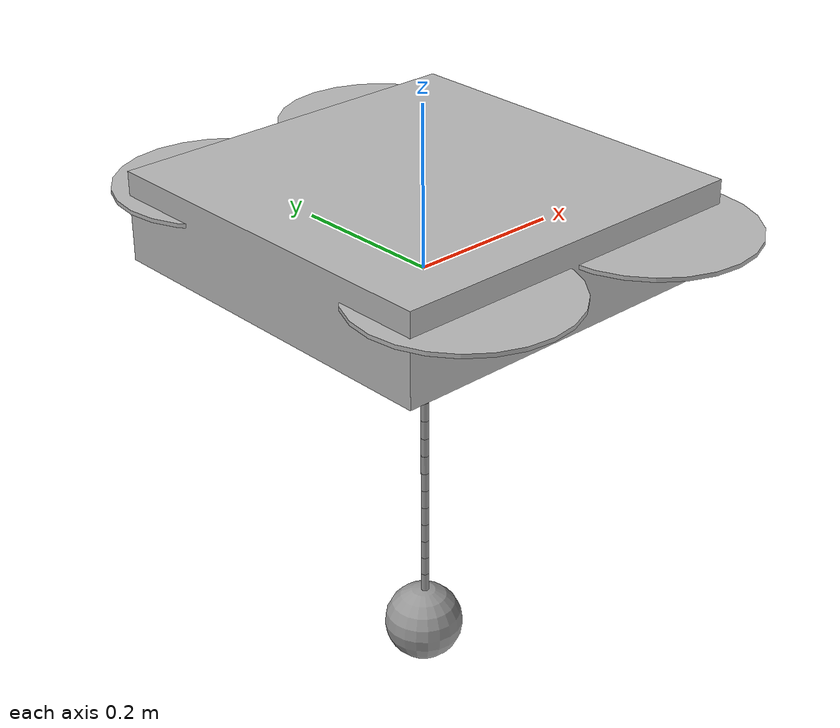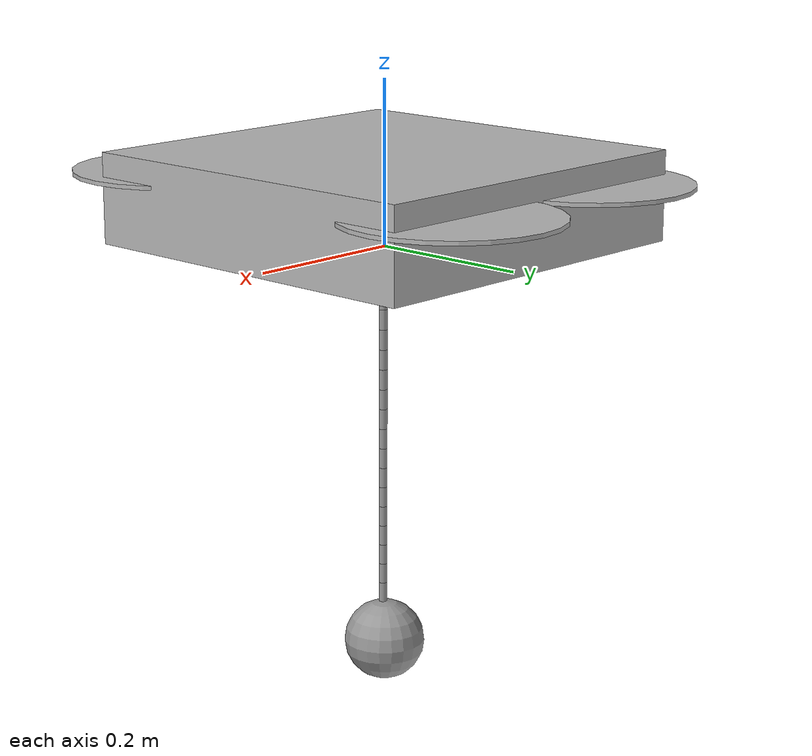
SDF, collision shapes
<?xml version="1.0" ?>
<sdf version='1.5'>
  <model name='iris_load_test'>
    <include>
      <uri>model://iris</uri>
      <pose> 0 0 0.06 0 0 0 </pose>
    </include>
    <include>
      <uri>model://cable</uri>
      <pose> 0 0 0.06 -1.5707 0 0 </pose>
    </include>
    <include>
      <uri>model://payload</uri>
      <pose> 0 0 -0.5025 0 0 0 </pose>
    </include>
    <joint name="iris_cable_joint" type="revolute">
        <child>iris::base_link</child>
        <parent>cable::link_1</parent>
        <pose> 0 0 0 0 0 0 </pose>
        <axis>
        <xyz>1 0 0</xyz>
        <limit>
          <lower>-1.79769e+308</lower>
          <upper>1.79769e+308</upper>
          <effort>-1</effort>
          <velocity>-1</velocity>
        </limit>
        <dynamics>
          <spring_reference>0</spring_reference>
          <spring_stiffness>0</spring_stiffness>
          <damping>0.5</damping>
        </dynamics>
      </axis>
      <physics>
        <ode>
          <implicit_spring_damper>1</implicit_spring_damper>
          <limit>
            <cfm>0</cfm>
            <erp>0.2</erp> <!-- changing to higher seems to improve realism-->
          </limit>
          <suspension>
            <cfm>0</cfm>
            <erp>0.2</erp>
          </suspension>
        </ode>
      </physics>
    </joint>
    <joint name='cable_payload_joint' type='revolute'>
      <parent>cable::link_20</parent>
      <child>payload::payload_link</child>
      <pose>0 0 0.05 0 -0 0</pose>
      <axis>
        <xyz>1 0 0</xyz>
        <limit>
          <lower>-1.79769e+308</lower>
          <upper>1.79769e+308</upper>
          <effort>-1</effort>
          <velocity>-1</velocity>
        </limit>
        <dynamics>
          <spring_reference>0</spring_reference>
          <spring_stiffness>0</spring_stiffness>
          <damping>0.5</damping>
        </dynamics>
      </axis>
      <physics>
        <ode>
          <implicit_spring_damper>1</implicit_spring_damper>
          <limit>
            <cfm>0</cfm>
            <erp>0.2</erp>
          </limit>
          <suspension>
            <cfm>0</cfm>
            <erp>0.2</erp>
          </suspension>
        </ode>
      </physics>
    </joint>
  </model>
</sdf>

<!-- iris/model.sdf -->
<!-- DO NOT EDIT: Generated from iris.sdf.jinja -->
<sdf version='1.6'>
  <model name='iris'>
    <link name='base_link'>
      <pose>0 0 0 0 0 0</pose>
      <inertial>
        <pose>0 0 0 0 0 0</pose>
        <mass>1.5</mass>
        <inertia>
          <ixx>0.029125</ixx>
          <ixy>0</ixy>
          <ixz>0</ixz>
          <iyy>0.029125</iyy>
          <iyz>0</iyz>
          <izz>0.055225</izz>
        </inertia>
      </inertial>
      <collision name='base_link_inertia_collision'>
        <pose>0 0 0 0 0 0</pose>
        <geometry>
          <box>
            <size>0.47 0.47 0.11</size>
          </box>
        </geometry>
        <surface>
          <contact>
            <ode>
              <min_depth>0.001</min_depth>
              <max_vel>0</max_vel>
            </ode>
          </contact>
          <friction>
            <ode/>
          </friction>
        </surface>
      </collision>
      <visual name='base_link_inertia_visual'>
        <pose>0 0 0 0 0 0</pose>
        <geometry>
          <mesh>
            <scale>1 1 1</scale>
            <uri>model://iris/meshes/iris.stl</uri>
          </mesh>
        </geometry>
      </visual>
      <gravity>1</gravity>
      <velocity_decay/>
    </link>
    <link name='/imu_link'>
      <pose>0 0 0 0 0 0</pose>
      <inertial>
        <pose>0 0 0 0 0 0</pose>
        <mass>0.015</mass>
        <inertia>
          <ixx>1e-05</ixx>
          <ixy>0</ixy>
          <ixz>0</ixz>
          <iyy>1e-05</iyy>
          <iyz>0</iyz>
          <izz>1e-05</izz>
        </inertia>
      </inertial>
    </link>
    <joint name='/imu_joint' type='revolute'>
      <child>/imu_link</child>
      <parent>base_link</parent>
      <axis>
        <xyz>1 0 0</xyz>
        <limit>
          <lower>0</lower>
          <upper>0</upper>
          <effort>0</effort>
          <velocity>0</velocity>
        </limit>
        <dynamics>
          <spring_reference>0</spring_reference>
          <spring_stiffness>0</spring_stiffness>
        </dynamics>
        <use_parent_model_frame>1</use_parent_model_frame>
      </axis>
    </joint>
    <link name='rotor_0'>
      <pose>0.13 -0.22 0.023 0 0 0</pose>
      <inertial>
        <pose>0 0 0 0 0 0</pose>
        <mass>0.005</mass>
        <inertia>
          <ixx>9.75e-07</ixx>
          <ixy>0</ixy>
          <ixz>0</ixz>
          <iyy>0.000273104</iyy>
          <iyz>0</iyz>
          <izz>0.000274004</izz>
        </inertia>
      </inertial>
      <collision name='rotor_0_collision'>
        <pose>0 0 0 0 0 0</pose>
        <geometry>
          <cylinder>
            <length>0.005</length>
            <radius>0.128</radius>
          </cylinder>
        </geometry>
        <surface>
          <contact>
            <ode/>
          </contact>
          <friction>
            <ode/>
          </friction>
        </surface>
      </collision>
      <visual name='rotor_0_visual'>
        <pose>0 0 0 0 0 0</pose>
        <geometry>
          <mesh>
            <scale>1 1 1</scale>
            <uri>model://iris/meshes/iris_prop_ccw.dae</uri>
          </mesh>
        </geometry>
      </visual>
      <gravity>1</gravity>
      <velocity_decay/>
    </link>
    <joint name='rotor_0_joint' type='revolute'>
      <child>rotor_0</child>
      <parent>base_link</parent>
      <axis>
        <xyz>0 0 1</xyz>
        <limit>
          <lower>-1e+16</lower>
          <upper>1e+16</upper>
        </limit>
        <dynamics>
          <spring_reference>0</spring_reference>
          <spring_stiffness>0</spring_stiffness>
        </dynamics>
        <use_parent_model_frame>1</use_parent_model_frame>
      </axis>
    </joint>
    <link name='rotor_1'>
      <pose>-0.13 0.2 0.023 0 0 0</pose>
      <inertial>
        <pose>0 0 0 0 0 0</pose>
        <mass>0.005</mass>
        <inertia>
          <ixx>9.75e-07</ixx>
          <ixy>0</ixy>
          <ixz>0</ixz>
          <iyy>0.000273104</iyy>
          <iyz>0</iyz>
          <izz>0.000274004</izz>
        </inertia>
      </inertial>
      <collision name='rotor_1_collision'>
        <pose>0 0 0 0 0 0</pose>
        <geometry>
          <cylinder>
            <length>0.005</length>
            <radius>0.128</radius>
          </cylinder>
        </geometry>
        <surface>
          <contact>
            <ode/>
          </contact>
          <friction>
            <ode/>
          </friction>
        </surface>
      </collision>
      <visual name='rotor_1_visual'>
        <pose>0 0 0 0 0 0</pose>
        <geometry>
          <mesh>
            <scale>1 1 1</scale>
            <uri>model://iris/meshes/iris_prop_ccw.dae</uri>
          </mesh>
        </geometry>
      </visual>
      <gravity>1</gravity>
      <velocity_decay/>
    </link>
    <joint name='rotor_1_joint' type='revolute'>
      <child>rotor_1</child>
      <parent>base_link</parent>
      <axis>
        <xyz>0 0 1</xyz>
        <limit>
          <lower>-1e+16</lower>
          <upper>1e+16</upper>
        </limit>
        <dynamics>
          <spring_reference>0</spring_reference>
          <spring_stiffness>0</spring_stiffness>
        </dynamics>
        <use_parent_model_frame>1</use_parent_model_frame>
      </axis>
    </joint>
    <link name='rotor_2'>
      <pose>0.13 0.22 0.023 0 0 0</pose>
      <inertial>
        <pose>0 0 0 0 0 0</pose>
        <mass>0.005</mass>
        <inertia>
          <ixx>9.75e-07</ixx>
          <ixy>0</ixy>
          <ixz>0</ixz>
          <iyy>0.000273104</iyy>
          <iyz>0</iyz>
          <izz>0.000274004</izz>
        </inertia>
      </inertial>
      <collision name='rotor_2_collision'>
        <pose>0 0 0 0 0 0</pose>
        <geometry>
          <cylinder>
            <length>0.005</length>
            <radius>0.128</radius>
          </cylinder>
        </geometry>
        <surface>
          <contact>
            <ode/>
          </contact>
          <friction>
            <ode/>
          </friction>
        </surface>
      </collision>
      <visual name='rotor_2_visual'>
        <pose>0 0 0 0 0 0</pose>
        <geometry>
          <mesh>
            <scale>1 1 1</scale>
            <uri>model://iris/meshes/iris_prop_cw.dae</uri>
          </mesh>
        </geometry>
      </visual>
      <gravity>1</gravity>
      <velocity_decay/>
    </link>
    <joint name='rotor_2_joint' type='revolute'>
      <child>rotor_2</child>
      <parent>base_link</parent>
      <axis>
        <xyz>0 0 1</xyz>
        <limit>
          <lower>-1e+16</lower>
          <upper>1e+16</upper>
        </limit>
        <dynamics>
          <spring_reference>0</spring_reference>
          <spring_stiffness>0</spring_stiffness>
        </dynamics>
        <use_parent_model_frame>1</use_parent_model_frame>
      </axis>
    </joint>
    <link name='rotor_3'>
      <pose>-0.13 -0.2 0.023 0 0 0</pose>
      <inertial>
        <pose>0 0 0 0 0 0</pose>
        <mass>0.005</mass>
        <inertia>
          <ixx>9.75e-07</ixx>
          <ixy>0</ixy>
          <ixz>0</ixz>
          <iyy>0.000273104</iyy>
          <iyz>0</iyz>
          <izz>0.000274004</izz>
        </inertia>
      </inertial>
      <collision name='rotor_3_collision'>
        <pose>0 0 0 0 0 0</pose>
        <geometry>
          <cylinder>
            <length>0.005</length>
            <radius>0.128</radius>
          </cylinder>
        </geometry>
        <surface>
          <contact>
            <ode/>
          </contact>
          <friction>
            <ode/>
          </friction>
        </surface>
      </collision>
      <visual name='rotor_3_visual'>
        <pose>0 0 0 0 0 0</pose>
        <geometry>
          <mesh>
            <scale>1 1 1</scale>
            <uri>model://iris/meshes/iris_prop_cw.dae</uri>
          </mesh>
        </geometry>
      </visual>
      <gravity>1</gravity>
      <velocity_decay/>
    </link>
    <joint name='rotor_3_joint' type='revolute'>
      <child>rotor_3</child>
      <parent>base_link</parent>
      <axis>
        <xyz>0 0 1</xyz>
        <limit>
          <lower>-1e+16</lower>
          <upper>1e+16</upper>
        </limit>
        <dynamics>
          <spring_reference>0</spring_reference>
          <spring_stiffness>0</spring_stiffness>
        </dynamics>
        <use_parent_model_frame>1</use_parent_model_frame>
      </axis>
    </joint>
    <plugin name='rosbag' filename='libgazebo_multirotor_base_plugin.so'>
      <robotNamespace/>
      <linkName>base_link</linkName>
      <rotorVelocitySlowdownSim>10</rotorVelocitySlowdownSim>
    </plugin>
    <plugin name='front_right_motor_model' filename='libgazebo_motor_model.so'>
      <robotNamespace/>
      <jointName>rotor_0_joint</jointName>
      <linkName>rotor_0</linkName>
      <turningDirection>ccw</turningDirection>
      <timeConstantUp>0.0125</timeConstantUp>
      <timeConstantDown>0.025</timeConstantDown>
      <maxRotVelocity>1100</maxRotVelocity>
      <motorConstant>5.84e-06</motorConstant>
      <momentConstant>0.06</momentConstant>
      <commandSubTopic>/gazebo/command/motor_speed</commandSubTopic>
      <motorNumber>0</motorNumber>
      <rotorDragCoefficient>0.000175</rotorDragCoefficient>
      <rollingMomentCoefficient>1e-06</rollingMomentCoefficient>
      <motorSpeedPubTopic>/motor_speed/0</motorSpeedPubTopic>
      <rotorVelocitySlowdownSim>10</rotorVelocitySlowdownSim>
    </plugin>
    <plugin name='back_left_motor_model' filename='libgazebo_motor_model.so'>
      <robotNamespace/>
      <jointName>rotor_1_joint</jointName>
      <linkName>rotor_1</linkName>
      <turningDirection>ccw</turningDirection>
      <timeConstantUp>0.0125</timeConstantUp>
      <timeConstantDown>0.025</timeConstantDown>
      <maxRotVelocity>1100</maxRotVelocity>
      <motorConstant>5.84e-06</motorConstant>
      <momentConstant>0.06</momentConstant>
      <commandSubTopic>/gazebo/command/motor_speed</commandSubTopic>
      <motorNumber>1</motorNumber>
      <rotorDragCoefficient>0.000175</rotorDragCoefficient>
      <rollingMomentCoefficient>1e-06</rollingMomentCoefficient>
      <motorSpeedPubTopic>/motor_speed/1</motorSpeedPubTopic>
      <rotorVelocitySlowdownSim>10</rotorVelocitySlowdownSim>
    </plugin>
    <plugin name='front_left_motor_model' filename='libgazebo_motor_model.so'>
      <robotNamespace/>
      <jointName>rotor_2_joint</jointName>
      <linkName>rotor_2</linkName>
      <turningDirection>cw</turningDirection>
      <timeConstantUp>0.0125</timeConstantUp>
      <timeConstantDown>0.025</timeConstantDown>
      <maxRotVelocity>1100</maxRotVelocity>
      <motorConstant>5.84e-06</motorConstant>
      <momentConstant>0.06</momentConstant>
      <commandSubTopic>/gazebo/command/motor_speed</commandSubTopic>
      <motorNumber>2</motorNumber>
      <rotorDragCoefficient>0.000175</rotorDragCoefficient>
      <rollingMomentCoefficient>1e-06</rollingMomentCoefficient>
      <motorSpeedPubTopic>/motor_speed/2</motorSpeedPubTopic>
      <rotorVelocitySlowdownSim>10</rotorVelocitySlowdownSim>
    </plugin>
    <plugin name='back_right_motor_model' filename='libgazebo_motor_model.so'>
      <robotNamespace/>
      <jointName>rotor_3_joint</jointName>
      <linkName>rotor_3</linkName>
      <turningDirection>cw</turningDirection>
      <timeConstantUp>0.0125</timeConstantUp>
      <timeConstantDown>0.025</timeConstantDown>
      <maxRotVelocity>1100</maxRotVelocity>
      <motorConstant>5.84e-06</motorConstant>
      <momentConstant>0.06</momentConstant>
      <commandSubTopic>/gazebo/command/motor_speed</commandSubTopic>
      <motorNumber>3</motorNumber>
      <rotorDragCoefficient>0.000175</rotorDragCoefficient>
      <rollingMomentCoefficient>1e-06</rollingMomentCoefficient>
      <motorSpeedPubTopic>/motor_speed/3</motorSpeedPubTopic>
      <rotorVelocitySlowdownSim>10</rotorVelocitySlowdownSim>
    </plugin>
    <model name='gps0'>
      <link name='link'>
        <pose>0 0 0 0 0 0</pose>
        <inertial>
          <pose>0 0 0 0 0 0</pose>
          <mass>0.01</mass>
          <inertia>
            <ixx>2.1733e-06</ixx>
            <ixy>0</ixy>
            <ixz>0</ixz>
            <iyy>2.1733e-06</iyy>
            <iyz>0</iyz>
            <izz>1.8e-07</izz>
          </inertia>
        </inertial>
        <visual name='visual'>
          <geometry>
            <cylinder>
              <radius>0.01</radius>
              <length>0.002</length>
            </cylinder>
          </geometry>
        </visual>
        <sensor name='gps' type='gps'>
          <pose>0 0 0 0 0 0</pose>
          <plugin name='gps_plugin' filename='libgazebo_gps_plugin.so'>
            <robotNamespace/>
            <gpsNoise>1</gpsNoise>
            <gpsXYRandomWalk>2.0</gpsXYRandomWalk>
            <gpsZRandomWalk>4.0</gpsZRandomWalk>
            <gpsXYNoiseDensity>0.0002</gpsXYNoiseDensity>
            <gpsZNoiseDensity>0.0004</gpsZNoiseDensity>
            <gpsVXYNoiseDensity>0.2</gpsVXYNoiseDensity>
            <gpsVZNoiseDensity>0.4</gpsVZNoiseDensity>
          </plugin>
        </sensor>
      </link>
    </model>
    <joint name='gps0_joint' type='fixed'>
      <parent>base_link</parent>
      <child>gps0::link</child>
    </joint>
    <plugin name='groundtruth_plugin' filename='libgazebo_groundtruth_plugin.so'>
      <robotNamespace/>
    </plugin>
    <plugin name='magnetometer_plugin' filename='libgazebo_magnetometer_plugin.so'>
      <robotNamespace/>
      <pubRate>100</pubRate>
      <noiseDensity>0.0004</noiseDensity>
      <randomWalk>6.4e-06</randomWalk>
      <biasCorrelationTime>600</biasCorrelationTime>
      <magTopic>/mag</magTopic>
    </plugin>
    <plugin name='barometer_plugin' filename='libgazebo_barometer_plugin.so'>
      <robotNamespace/>
      <pubRate>50</pubRate>
      <baroTopic>/baro</baroTopic>
      <baroDriftPaPerSec>0</baroDriftPaPerSec>
    </plugin>
    <plugin name='mavlink_interface' filename='libgazebo_mavlink_interface.so'>
      <robotNamespace/>
      <imuSubTopic>/imu</imuSubTopic>
      <magSubTopic>/mag</magSubTopic>
      <baroSubTopic>/baro</baroSubTopic>
      <mavlink_addr>INADDR_ANY</mavlink_addr>
      <mavlink_tcp_port>{{ mavlink_tcp_port }}</mavlink_tcp_port>
      <mavlink_udp_port>{{ mavlink_udp_port }}</mavlink_udp_port>
      <serialEnabled>{{ serial_enabled }}</serialEnabled>
      <serialDevice>{{ serial_device }}</serialDevice>
      <baudRate>{{ serial_baudrate }}</baudRate>
      <qgc_addr>INADDR_ANY</qgc_addr>
      <qgc_udp_port>14550</qgc_udp_port>
      <sdk_addr>INADDR_ANY</sdk_addr>
      <sdk_udp_port>14540</sdk_udp_port>
      <hil_mode>{{ hil_mode }}</hil_mode>
      <hil_state_level>0</hil_state_level>
      <send_vision_estimation>0</send_vision_estimation>
      <send_odometry>1</send_odometry>
      <enable_lockstep>1</enable_lockstep>
      <use_tcp>1</use_tcp>
      <motorSpeedCommandPubTopic>/gazebo/command/motor_speed</motorSpeedCommandPubTopic>
      <control_channels>
        <channel name='rotor1'>
          <input_index>0</input_index>
          <input_offset>0</input_offset>
          <input_scaling>1000</input_scaling>
          <zero_position_disarmed>0</zero_position_disarmed>
          <zero_position_armed>100</zero_position_armed>
          <joint_control_type>velocity</joint_control_type>
        </channel>
        <channel name='rotor2'>
          <input_index>1</input_index>
          <input_offset>0</input_offset>
          <input_scaling>1000</input_scaling>
          <zero_position_disarmed>0</zero_position_disarmed>
          <zero_position_armed>100</zero_position_armed>
          <joint_control_type>velocity</joint_control_type>
        </channel>
        <channel name='rotor3'>
          <input_index>2</input_index>
          <input_offset>0</input_offset>
          <input_scaling>1000</input_scaling>
          <zero_position_disarmed>0</zero_position_disarmed>
          <zero_position_armed>100</zero_position_armed>
          <joint_control_type>velocity</joint_control_type>
        </channel>
        <channel name='rotor4'>
          <input_index>3</input_index>
          <input_offset>0</input_offset>
          <input_scaling>1000</input_scaling>
          <zero_position_disarmed>0</zero_position_disarmed>
          <zero_position_armed>100</zero_position_armed>
          <joint_control_type>velocity</joint_control_type>
        </channel>
        <channel name='rotor5'>
          <input_index>4</input_index>
          <input_offset>1</input_offset>
          <input_scaling>324.6</input_scaling>
          <zero_position_disarmed>0</zero_position_disarmed>
          <zero_position_armed>0</zero_position_armed>
          <joint_control_type>velocity</joint_control_type>
          <joint_control_pid>
            <p>0.1</p>
            <i>0</i>
            <d>0</d>
            <iMax>0.0</iMax>
            <iMin>0.0</iMin>
            <cmdMax>2</cmdMax>
            <cmdMin>-2</cmdMin>
          </joint_control_pid>
          <joint_name>zephyr_delta_wing::propeller_joint</joint_name>
        </channel>
        <channel name='rotor6'>
          <input_index>5</input_index>
          <input_offset>0</input_offset>
          <input_scaling>0.524</input_scaling>
          <zero_position_disarmed>0</zero_position_disarmed>
          <zero_position_armed>0</zero_position_armed>
          <joint_control_type>position</joint_control_type>
          <joint_name>zephyr_delta_wing::flap_left_joint</joint_name>
          <joint_control_pid>
            <p>10.0</p>
            <i>0</i>
            <d>0</d>
            <iMax>0</iMax>
            <iMin>0</iMin>
            <cmdMax>20</cmdMax>
            <cmdMin>-20</cmdMin>
          </joint_control_pid>
        </channel>
        <channel name='rotor7'>
          <input_index>6</input_index>
          <input_offset>0</input_offset>
          <input_scaling>0.524</input_scaling>
          <zero_position_disarmed>0</zero_position_disarmed>
          <zero_position_armed>0</zero_position_armed>
          <joint_control_type>position</joint_control_type>
          <joint_name>zephyr_delta_wing::flap_right_joint</joint_name>
          <joint_control_pid>
            <p>10.0</p>
            <i>0</i>
            <d>0</d>
            <iMax>0</iMax>
            <iMin>0</iMin>
            <cmdMax>20</cmdMax>
            <cmdMin>-20</cmdMin>
          </joint_control_pid>
        </channel>
        <channel name='rotor8'>
          <input_index>7</input_index>
          <input_offset>0</input_offset>
          <input_scaling>0.524</input_scaling>
          <zero_position_disarmed>0</zero_position_disarmed>
          <zero_position_armed>0</zero_position_armed>
          <joint_control_type>position</joint_control_type>
        </channel>
      </control_channels>
    </plugin>
    <static>0</static>
    <plugin name='rotors_gazebo_imu_plugin' filename='libgazebo_imu_plugin.so'>
      <robotNamespace/>
      <linkName>/imu_link</linkName>
      <imuTopic>/imu</imuTopic>
      <gyroscopeNoiseDensity>0.00018665</gyroscopeNoiseDensity>
      <gyroscopeRandomWalk>3.8785e-05</gyroscopeRandomWalk>
      <gyroscopeBiasCorrelationTime>1000.0</gyroscopeBiasCorrelationTime>
      <gyroscopeTurnOnBiasSigma>0.0087</gyroscopeTurnOnBiasSigma>
      <accelerometerNoiseDensity>0.00186</accelerometerNoiseDensity>
      <accelerometerRandomWalk>0.006</accelerometerRandomWalk>
      <accelerometerBiasCorrelationTime>300.0</accelerometerBiasCorrelationTime>
      <accelerometerTurnOnBiasSigma>0.196</accelerometerTurnOnBiasSigma>
    </plugin>
  </model>
</sdf>

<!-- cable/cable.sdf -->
<sdf version='1.5'>
  <model name='cable'>

    <link name="link_1">    <!-- m = 0.1 used for plots-->
      <pose>0 0.025 -0.0025 1.5708 0 0</pose>
      <inertial>
        <mass> 0.0005 </mass>
        <inertia>
          <ixx>6.2500000000000005e-09</ixx>
          <ixy>0</ixy>
          <ixz>0</ixz>
          <iyy>6.2500000000000005e-09</iyy>
          <iyz>0</iyz>
          <izz>1.0729166666666668e-07</izz>
        </inertia>
        <pose>0 0 0 0 0 0</pose>
      </inertial>
      <self_collide>0</self_collide>
      <enable_wind>0</enable_wind>
      <kinematic>0</kinematic>
      <gravity>1</gravity>
      <visual name='visual_1'>
        <geometry>
          <cylinder>
            <radius>0.005</radius>
            <length>0.025</length>
          </cylinder>
        </geometry>
        <material>
          <script>
            <name>Gazebo/Grey</name>
            <uri>file://media/materials/scripts/gazebo.material</uri>
          </script>
          <shader type='pixel'>
            <normal_map>__default__</normal_map>
          </shader>
          <ambient>0.3 0.3 0.3 1</ambient>
          <diffuse>0.7 0.7 0.7 1</diffuse>
          <specular>0.01 0.01 0.01 1</specular>
          <emissive>0 0 0 1</emissive>
        </material>
        <pose>0 0 0 0 -0 0</pose>
        <transparency>0</transparency>
        <cast_shadows>1</cast_shadows>
      </visual>
      <visual name='sphere'>
        <geometry>
          <sphere>
            <radius>0.005</radius>
          </sphere>
        </geometry>
        <pose>0 0 -0.0125 0 0 0</pose>
        <material>
          <script>
            <name>Gazebo/Grey</name>
            <uri>file://media/materials/scripts/gazebo.material</uri>
          </script>
          <shader type='pixel'>
            <normal_map>__default__</normal_map>
          </shader>
          <ambient>0.3 0.3 0.3 1</ambient>
          <diffuse>0.7 0.7 0.7 1</diffuse>
          <specular>0.01 0.01 0.01 1</specular>
          <emissive>0 0 0 1</emissive>
        </material>
        <transparency>0</transparency>
        <cast_shadows>1</cast_shadows>
      </visual>
      <collision name='collision_1'>
        <laser_retro>0</laser_retro>
        <max_contacts>10</max_contacts>
        <pose>0 0 0 0 -0 0</pose>
        <geometry>
          <cylinder>
            <radius>0.005</radius>
            <length>0.025</length>
          </cylinder>
        </geometry>
        <surface>
          <friction>
            <ode>
              <mu>1</mu>
              <mu2>1</mu2>
              <fdir1>0 0 0</fdir1>
              <slip1>0</slip1>
              <slip2>0</slip2>
            </ode>
            <torsional>
              <coefficient>1</coefficient>
              <patch_radius>0</patch_radius>
              <surface_radius>0</surface_radius>
              <use_patch_radius>1</use_patch_radius>
              <ode>
                <slip>0</slip>
              </ode>
            </torsional>
          </friction>
          <bounce>
            <restitution_coefficient>0</restitution_coefficient>
            <threshold>1e+06</threshold>
          </bounce>
          <contact>
            <collide_bitmask>0</collide_bitmask>
            <ode>
              <soft_cfm>0</soft_cfm>
              <soft_erp>0.2</soft_erp>
              <kp>1e+13</kp>
              <kd>1</kd>
              <max_vel>0.01</max_vel>
              <min_depth>0</min_depth>
            </ode>
            <bullet>
              <split_impulse>1</split_impulse>
              <split_impulse_penetration_threshold>-0.01</split_impulse_penetration_threshold>
              <soft_cfm>0</soft_cfm>
              <soft_erp>0.2</soft_erp>
              <kp>1e+13</kp>
              <kd>1</kd>
            </bullet>
          </contact>
        </surface>
      </collision>
      </link>
    <link name="link_2">    <!-- m = 0.1 used for plots-->
      <pose>0 0.05 -0.0025 1.5708 0 0</pose>
      <inertial>
        <mass> 0.0005 </mass>
        <inertia>
          <ixx>6.2500000000000005e-09</ixx>
          <ixy>0</ixy>
          <ixz>0</ixz>
          <iyy>6.2500000000000005e-09</iyy>
          <iyz>0</iyz>
          <izz>1.0729166666666668e-07</izz>
        </inertia>
        <pose>0 0 0 0 0 0</pose>
      </inertial>
      <self_collide>0</self_collide>
      <enable_wind>0</enable_wind>
      <kinematic>0</kinematic>
      <gravity>1</gravity>
      <visual name='visual_2'>
        <geometry>
          <cylinder>
            <radius>0.005</radius>
            <length>0.025</length>
          </cylinder>
        </geometry>
        <material>
          <script>
            <name>Gazebo/Grey</name>
            <uri>file://media/materials/scripts/gazebo.material</uri>
          </script>
          <shader type='pixel'>
            <normal_map>__default__</normal_map>
          </shader>
          <ambient>0.3 0.3 0.3 1</ambient>
          <diffuse>0.7 0.7 0.7 1</diffuse>
          <specular>0.01 0.01 0.01 1</specular>
          <emissive>0 0 0 1</emissive>
        </material>
        <pose>0 0 0 0 -0 0</pose>
        <transparency>0</transparency>
        <cast_shadows>1</cast_shadows>
      </visual>
      <visual name='sphere'>
        <geometry>
          <sphere>
            <radius>0.005</radius>
          </sphere>
        </geometry>
        <pose>0 0 -0.0125 0 0 0</pose>
        <material>
          <script>
            <name>Gazebo/Grey</name>
            <uri>file://media/materials/scripts/gazebo.material</uri>
          </script>
          <shader type='pixel'>
            <normal_map>__default__</normal_map>
          </shader>
          <ambient>0.3 0.3 0.3 1</ambient>
          <diffuse>0.7 0.7 0.7 1</diffuse>
          <specular>0.01 0.01 0.01 1</specular>
          <emissive>0 0 0 1</emissive>
        </material>
        <transparency>0</transparency>
        <cast_shadows>1</cast_shadows>
      </visual>
      <collision name='collision_2'>
        <laser_retro>0</laser_retro>
        <max_contacts>10</max_contacts>
        <pose>0 0 0 0 -0 0</pose>
        <geometry>
          <cylinder>
            <radius>0.005</radius>
            <length>0.025</length>
          </cylinder>
        </geometry>
        <surface>
          <friction>
            <ode>
              <mu>1</mu>
              <mu2>1</mu2>
              <fdir1>0 0 0</fdir1>
              <slip1>0</slip1>
              <slip2>0</slip2>
            </ode>
            <torsional>
              <coefficient>1</coefficient>
              <patch_radius>0</patch_radius>
              <surface_radius>0</surface_radius>
              <use_patch_radius>1</use_patch_radius>
              <ode>
                <slip>0</slip>
              </ode>
            </torsional>
          </friction>
          <bounce>
            <restitution_coefficient>0</restitution_coefficient>
            <threshold>1e+06</threshold>
          </bounce>
          <contact>
            <collide_bitmask>0</collide_bitmask>
            <ode>
              <soft_cfm>0</soft_cfm>
              <soft_erp>0.2</soft_erp>
              <kp>1e+13</kp>
              <kd>1</kd>
              <max_vel>0.01</max_vel>
              <min_depth>0</min_depth>
            </ode>
            <bullet>
              <split_impulse>1</split_impulse>
              <split_impulse_penetration_threshold>-0.01</split_impulse_penetration_threshold>
              <soft_cfm>0</soft_cfm>
              <soft_erp>0.2</soft_erp>
              <kp>1e+13</kp>
              <kd>1</kd>
            </bullet>
          </contact>
        </surface>
      </collision>
      </link>
    <link name="link_3">    <!-- m = 0.1 used for plots-->
      <pose>0 0.07500000000000001 -0.0025 1.5708 0 0</pose>
      <inertial>
        <mass> 0.0005 </mass>
        <inertia>
          <ixx>6.2500000000000005e-09</ixx>
          <ixy>0</ixy>
          <ixz>0</ixz>
          <iyy>6.2500000000000005e-09</iyy>
          <iyz>0</iyz>
          <izz>1.0729166666666668e-07</izz>
        </inertia>
        <pose>0 0 0 0 0 0</pose>
      </inertial>
      <self_collide>0</self_collide>
      <enable_wind>0</enable_wind>
      <kinematic>0</kinematic>
      <gravity>1</gravity>
      <visual name='visual_3'>
        <geometry>
          <cylinder>
            <radius>0.005</radius>
            <length>0.025</length>
          </cylinder>
        </geometry>
        <material>
          <script>
            <name>Gazebo/Grey</name>
            <uri>file://media/materials/scripts/gazebo.material</uri>
          </script>
          <shader type='pixel'>
            <normal_map>__default__</normal_map>
          </shader>
          <ambient>0.3 0.3 0.3 1</ambient>
          <diffuse>0.7 0.7 0.7 1</diffuse>
          <specular>0.01 0.01 0.01 1</specular>
          <emissive>0 0 0 1</emissive>
        </material>
        <pose>0 0 0 0 -0 0</pose>
        <transparency>0</transparency>
        <cast_shadows>1</cast_shadows>
      </visual>
      <visual name='sphere'>
        <geometry>
          <sphere>
            <radius>0.005</radius>
          </sphere>
        </geometry>
        <pose>0 0 -0.0125 0 0 0</pose>
        <material>
          <script>
            <name>Gazebo/Grey</name>
            <uri>file://media/materials/scripts/gazebo.material</uri>
          </script>
          <shader type='pixel'>
            <normal_map>__default__</normal_map>
          </shader>
          <ambient>0.3 0.3 0.3 1</ambient>
          <diffuse>0.7 0.7 0.7 1</diffuse>
          <specular>0.01 0.01 0.01 1</specular>
          <emissive>0 0 0 1</emissive>
        </material>
        <transparency>0</transparency>
        <cast_shadows>1</cast_shadows>
      </visual>
      <collision name='collision_3'>
        <laser_retro>0</laser_retro>
        <max_contacts>10</max_contacts>
        <pose>0 0 0 0 -0 0</pose>
        <geometry>
          <cylinder>
            <radius>0.005</radius>
            <length>0.025</length>
          </cylinder>
        </geometry>
        <surface>
          <friction>
            <ode>
              <mu>1</mu>
              <mu2>1</mu2>
              <fdir1>0 0 0</fdir1>
              <slip1>0</slip1>
              <slip2>0</slip2>
            </ode>
            <torsional>
              <coefficient>1</coefficient>
              <patch_radius>0</patch_radius>
              <surface_radius>0</surface_radius>
              <use_patch_radius>1</use_patch_radius>
              <ode>
                <slip>0</slip>
              </ode>
            </torsional>
          </friction>
          <bounce>
            <restitution_coefficient>0</restitution_coefficient>
            <threshold>1e+06</threshold>
          </bounce>
          <contact>
            <collide_bitmask>0</collide_bitmask>
            <ode>
              <soft_cfm>0</soft_cfm>
              <soft_erp>0.2</soft_erp>
              <kp>1e+13</kp>
              <kd>1</kd>
              <max_vel>0.01</max_vel>
              <min_depth>0</min_depth>
            </ode>
            <bullet>
              <split_impulse>1</split_impulse>
              <split_impulse_penetration_threshold>-0.01</split_impulse_penetration_threshold>
              <soft_cfm>0</soft_cfm>
              <soft_erp>0.2</soft_erp>
              <kp>1e+13</kp>
              <kd>1</kd>
            </bullet>
          </contact>
        </surface>
      </collision>
      </link>
    <link name="link_4">    <!-- m = 0.1 used for plots-->
      <pose>0 0.1 -0.0025 1.5708 0 0</pose>
      <inertial>
        <mass> 0.0005 </mass>
        <inertia>
          <ixx>6.2500000000000005e-09</ixx>
          <ixy>0</ixy>
          <ixz>0</ixz>
          <iyy>6.2500000000000005e-09</iyy>
          <iyz>0</iyz>
          <izz>1.0729166666666668e-07</izz>
        </inertia>
        <pose>0 0 0 0 0 0</pose>
      </inertial>
      <self_collide>0</self_collide>
      <enable_wind>0</enable_wind>
      <kinematic>0</kinematic>
      <gravity>1</gravity>
      <visual name='visual_4'>
        <geometry>
          <cylinder>
            <radius>0.005</radius>
            <length>0.025</length>
          </cylinder>
        </geometry>
        <material>
          <script>
            <name>Gazebo/Grey</name>
            <uri>file://media/materials/scripts/gazebo.material</uri>
          </script>
          <shader type='pixel'>
            <normal_map>__default__</normal_map>
          </shader>
          <ambient>0.3 0.3 0.3 1</ambient>
          <diffuse>0.7 0.7 0.7 1</diffuse>
          <specular>0.01 0.01 0.01 1</specular>
          <emissive>0 0 0 1</emissive>
        </material>
        <pose>0 0 0 0 -0 0</pose>
        <transparency>0</transparency>
        <cast_shadows>1</cast_shadows>
      </visual>
      <visual name='sphere'>
        <geometry>
          <sphere>
            <radius>0.005</radius>
          </sphere>
        </geometry>
        <pose>0 0 -0.0125 0 0 0</pose>
        <material>
          <script>
            <name>Gazebo/Grey</name>
            <uri>file://media/materials/scripts/gazebo.material</uri>
          </script>
          <shader type='pixel'>
            <normal_map>__default__</normal_map>
          </shader>
          <ambient>0.3 0.3 0.3 1</ambient>
          <diffuse>0.7 0.7 0.7 1</diffuse>
          <specular>0.01 0.01 0.01 1</specular>
          <emissive>0 0 0 1</emissive>
        </material>
        <transparency>0</transparency>
        <cast_shadows>1</cast_shadows>
      </visual>
      <collision name='collision_4'>
        <laser_retro>0</laser_retro>
        <max_contacts>10</max_contacts>
        <pose>0 0 0 0 -0 0</pose>
        <geometry>
          <cylinder>
            <radius>0.005</radius>
            <length>0.025</length>
          </cylinder>
        </geometry>
        <surface>
          <friction>
            <ode>
              <mu>1</mu>
              <mu2>1</mu2>
              <fdir1>0 0 0</fdir1>
              <slip1>0</slip1>
              <slip2>0</slip2>
            </ode>
            <torsional>
              <coefficient>1</coefficient>
              <patch_radius>0</patch_radius>
              <surface_radius>0</surface_radius>
              <use_patch_radius>1</use_patch_radius>
              <ode>
                <slip>0</slip>
              </ode>
            </torsional>
          </friction>
          <bounce>
            <restitution_coefficient>0</restitution_coefficient>
            <threshold>1e+06</threshold>
          </bounce>
          <contact>
            <collide_bitmask>0</collide_bitmask>
            <ode>
              <soft_cfm>0</soft_cfm>
              <soft_erp>0.2</soft_erp>
              <kp>1e+13</kp>
              <kd>1</kd>
              <max_vel>0.01</max_vel>
              <min_depth>0</min_depth>
            </ode>
            <bullet>
              <split_impulse>1</split_impulse>
              <split_impulse_penetration_threshold>-0.01</split_impulse_penetration_threshold>
              <soft_cfm>0</soft_cfm>
              <soft_erp>0.2</soft_erp>
              <kp>1e+13</kp>
              <kd>1</kd>
            </bullet>
          </contact>
        </surface>
      </collision>
      </link>
    <link name="link_5">    <!-- m = 0.1 used for plots-->
      <pose>0 0.125 -0.0025 1.5708 0 0</pose>
      <inertial>
        <mass> 0.0005 </mass>
        <inertia>
          <ixx>6.2500000000000005e-09</ixx>
          <ixy>0</ixy>
          <ixz>0</ixz>
          <iyy>6.2500000000000005e-09</iyy>
          <iyz>0</iyz>
          <izz>1.0729166666666668e-07</izz>
        </inertia>
        <pose>0 0 0 0 0 0</pose>
      </inertial>
      <self_collide>0</self_collide>
      <enable_wind>0</enable_wind>
      <kinematic>0</kinematic>
      <gravity>1</gravity>
      <visual name='visual_5'>
        <geometry>
          <cylinder>
            <radius>0.005</radius>
            <length>0.025</length>
          </cylinder>
        </geometry>
        <material>
          <script>
            <name>Gazebo/Grey</name>
            <uri>file://media/materials/scripts/gazebo.material</uri>
          </script>
          <shader type='pixel'>
            <normal_map>__default__</normal_map>
          </shader>
          <ambient>0.3 0.3 0.3 1</ambient>
          <diffuse>0.7 0.7 0.7 1</diffuse>
          <specular>0.01 0.01 0.01 1</specular>
          <emissive>0 0 0 1</emissive>
        </material>
        <pose>0 0 0 0 -0 0</pose>
        <transparency>0</transparency>
        <cast_shadows>1</cast_shadows>
      </visual>
      <visual name='sphere'>
        <geometry>
          <sphere>
            <radius>0.005</radius>
          </sphere>
        </geometry>
        <pose>0 0 -0.0125 0 0 0</pose>
        <material>
          <script>
            <name>Gazebo/Grey</name>
            <uri>file://media/materials/scripts/gazebo.material</uri>
          </script>
          <shader type='pixel'>
            <normal_map>__default__</normal_map>
          </shader>
          <ambient>0.3 0.3 0.3 1</ambient>
          <diffuse>0.7 0.7 0.7 1</diffuse>
          <specular>0.01 0.01 0.01 1</specular>
          <emissive>0 0 0 1</emissive>
        </material>
        <transparency>0</transparency>
        <cast_shadows>1</cast_shadows>
      </visual>
      <collision name='collision_5'>
        <laser_retro>0</laser_retro>
        <max_contacts>10</max_contacts>
        <pose>0 0 0 0 -0 0</pose>
        <geometry>
          <cylinder>
            <radius>0.005</radius>
            <length>0.025</length>
          </cylinder>
        </geometry>
        <surface>
          <friction>
            <ode>
              <mu>1</mu>
              <mu2>1</mu2>
              <fdir1>0 0 0</fdir1>
              <slip1>0</slip1>
              <slip2>0</slip2>
            </ode>
            <torsional>
              <coefficient>1</coefficient>
              <patch_radius>0</patch_radius>
              <surface_radius>0</surface_radius>
              <use_patch_radius>1</use_patch_radius>
              <ode>
                <slip>0</slip>
              </ode>
            </torsional>
          </friction>
          <bounce>
            <restitution_coefficient>0</restitution_coefficient>
            <threshold>1e+06</threshold>
          </bounce>
          <contact>
            <collide_bitmask>0</collide_bitmask>
            <ode>
              <soft_cfm>0</soft_cfm>
              <soft_erp>0.2</soft_erp>
              <kp>1e+13</kp>
              <kd>1</kd>
              <max_vel>0.01</max_vel>
              <min_depth>0</min_depth>
            </ode>
            <bullet>
              <split_impulse>1</split_impulse>
              <split_impulse_penetration_threshold>-0.01</split_impulse_penetration_threshold>
              <soft_cfm>0</soft_cfm>
              <soft_erp>0.2</soft_erp>
              <kp>1e+13</kp>
              <kd>1</kd>
            </bullet>
          </contact>
        </surface>
      </collision>
      </link>
    <link name="link_6">    <!-- m = 0.1 used for plots-->
      <pose>0 0.15000000000000002 -0.0025 1.5708 0 0</pose>
      <inertial>
        <mass> 0.0005 </mass>
        <inertia>
          <ixx>6.2500000000000005e-09</ixx>
          <ixy>0</ixy>
          <ixz>0</ixz>
          <iyy>6.2500000000000005e-09</iyy>
          <iyz>0</iyz>
          <izz>1.0729166666666668e-07</izz>
        </inertia>
        <pose>0 0 0 0 0 0</pose>
      </inertial>
      <self_collide>0</self_collide>
      <enable_wind>0</enable_wind>
      <kinematic>0</kinematic>
      <gravity>1</gravity>
      <visual name='visual_6'>
        <geometry>
          <cylinder>
            <radius>0.005</radius>
            <length>0.025</length>
          </cylinder>
        </geometry>
        <material>
          <script>
            <name>Gazebo/Grey</name>
            <uri>file://media/materials/scripts/gazebo.material</uri>
          </script>
          <shader type='pixel'>
            <normal_map>__default__</normal_map>
          </shader>
          <ambient>0.3 0.3 0.3 1</ambient>
          <diffuse>0.7 0.7 0.7 1</diffuse>
          <specular>0.01 0.01 0.01 1</specular>
          <emissive>0 0 0 1</emissive>
        </material>
        <pose>0 0 0 0 -0 0</pose>
        <transparency>0</transparency>
        <cast_shadows>1</cast_shadows>
      </visual>
      <visual name='sphere'>
        <geometry>
          <sphere>
            <radius>0.005</radius>
          </sphere>
        </geometry>
        <pose>0 0 -0.0125 0 0 0</pose>
        <material>
          <script>
            <name>Gazebo/Grey</name>
            <uri>file://media/materials/scripts/gazebo.material</uri>
          </script>
          <shader type='pixel'>
            <normal_map>__default__</normal_map>
          </shader>
          <ambient>0.3 0.3 0.3 1</ambient>
          <diffuse>0.7 0.7 0.7 1</diffuse>
          <specular>0.01 0.01 0.01 1</specular>
          <emissive>0 0 0 1</emissive>
        </material>
        <transparency>0</transparency>
        <cast_shadows>1</cast_shadows>
      </visual>
      <collision name='collision_6'>
        <laser_retro>0</laser_retro>
        <max_contacts>10</max_contacts>
        <pose>0 0 0 0 -0 0</pose>
        <geometry>
          <cylinder>
            <radius>0.005</radius>
            <length>0.025</length>
          </cylinder>
        </geometry>
        <surface>
          <friction>
            <ode>
              <mu>1</mu>
              <mu2>1</mu2>
              <fdir1>0 0 0</fdir1>
              <slip1>0</slip1>
              <slip2>0</slip2>
            </ode>
            <torsional>
              <coefficient>1</coefficient>
              <patch_radius>0</patch_radius>
              <surface_radius>0</surface_radius>
              <use_patch_radius>1</use_patch_radius>
              <ode>
                <slip>0</slip>
              </ode>
            </torsional>
          </friction>
          <bounce>
            <restitution_coefficient>0</restitution_coefficient>
            <threshold>1e+06</threshold>
          </bounce>
          <contact>
            <collide_bitmask>0</collide_bitmask>
            <ode>
              <soft_cfm>0</soft_cfm>
              <soft_erp>0.2</soft_erp>
              <kp>1e+13</kp>
              <kd>1</kd>
              <max_vel>0.01</max_vel>
              <min_depth>0</min_depth>
            </ode>
            <bullet>
              <split_impulse>1</split_impulse>
              <split_impulse_penetration_threshold>-0.01</split_impulse_penetration_threshold>
              <soft_cfm>0</soft_cfm>
              <soft_erp>0.2</soft_erp>
              <kp>1e+13</kp>
              <kd>1</kd>
            </bullet>
          </contact>
        </surface>
      </collision>
      </link>
    <link name="link_7">    <!-- m = 0.1 used for plots-->
      <pose>0 0.17500000000000002 -0.0025 1.5708 0 0</pose>
      <inertial>
        <mass> 0.0005 </mass>
        <inertia>
          <ixx>6.2500000000000005e-09</ixx>
          <ixy>0</ixy>
          <ixz>0</ixz>
          <iyy>6.2500000000000005e-09</iyy>
          <iyz>0</iyz>
          <izz>1.0729166666666668e-07</izz>
        </inertia>
        <pose>0 0 0 0 0 0</pose>
      </inertial>
      <self_collide>0</self_collide>
      <enable_wind>0</enable_wind>
      <kinematic>0</kinematic>
      <gravity>1</gravity>
      <visual name='visual_7'>
        <geometry>
          <cylinder>
            <radius>0.005</radius>
            <length>0.025</length>
          </cylinder>
        </geometry>
        <material>
          <script>
            <name>Gazebo/Grey</name>
            <uri>file://media/materials/scripts/gazebo.material</uri>
          </script>
          <shader type='pixel'>
            <normal_map>__default__</normal_map>
          </shader>
          <ambient>0.3 0.3 0.3 1</ambient>
          <diffuse>0.7 0.7 0.7 1</diffuse>
          <specular>0.01 0.01 0.01 1</specular>
          <emissive>0 0 0 1</emissive>
        </material>
        <pose>0 0 0 0 -0 0</pose>
        <transparency>0</transparency>
        <cast_shadows>1</cast_shadows>
      </visual>
      <visual name='sphere'>
        <geometry>
          <sphere>
            <radius>0.005</radius>
          </sphere>
        </geometry>
        <pose>0 0 -0.0125 0 0 0</pose>
        <material>
          <script>
            <name>Gazebo/Grey</name>
            <uri>file://media/materials/scripts/gazebo.material</uri>
          </script>
          <shader type='pixel'>
            <normal_map>__default__</normal_map>
          </shader>
          <ambient>0.3 0.3 0.3 1</ambient>
          <diffuse>0.7 0.7 0.7 1</diffuse>
          <specular>0.01 0.01 0.01 1</specular>
          <emissive>0 0 0 1</emissive>
        </material>
        <transparency>0</transparency>
        <cast_shadows>1</cast_shadows>
      </visual>
      <collision name='collision_7'>
        <laser_retro>0</laser_retro>
        <max_contacts>10</max_contacts>
        <pose>0 0 0 0 -0 0</pose>
        <geometry>
          <cylinder>
            <radius>0.005</radius>
            <length>0.025</length>
          </cylinder>
        </geometry>
        <surface>
          <friction>
            <ode>
              <mu>1</mu>
              <mu2>1</mu2>
              <fdir1>0 0 0</fdir1>
              <slip1>0</slip1>
              <slip2>0</slip2>
            </ode>
            <torsional>
              <coefficient>1</coefficient>
              <patch_radius>0</patch_radius>
              <surface_radius>0</surface_radius>
              <use_patch_radius>1</use_patch_radius>
              <ode>
                <slip>0</slip>
              </ode>
            </torsional>
          </friction>
          <bounce>
            <restitution_coefficient>0</restitution_coefficient>
            <threshold>1e+06</threshold>
          </bounce>
          <contact>
            <collide_bitmask>0</collide_bitmask>
            <ode>
              <soft_cfm>0</soft_cfm>
              <soft_erp>0.2</soft_erp>
              <kp>1e+13</kp>
              <kd>1</kd>
              <max_vel>0.01</max_vel>
              <min_depth>0</min_depth>
            </ode>
            <bullet>
              <split_impulse>1</split_impulse>
              <split_impulse_penetration_threshold>-0.01</split_impulse_penetration_threshold>
              <soft_cfm>0</soft_cfm>
              <soft_erp>0.2</soft_erp>
              <kp>1e+13</kp>
              <kd>1</kd>
            </bullet>
          </contact>
        </surface>
      </collision>
      </link>
    <link name="link_8">    <!-- m = 0.1 used for plots-->
      <pose>0 0.2 -0.0025 1.5708 0 0</pose>
      <inertial>
        <mass> 0.0005 </mass>
        <inertia>
          <ixx>6.2500000000000005e-09</ixx>
          <ixy>0</ixy>
          <ixz>0</ixz>
          <iyy>6.2500000000000005e-09</iyy>
          <iyz>0</iyz>
          <izz>1.0729166666666668e-07</izz>
        </inertia>
        <pose>0 0 0 0 0 0</pose>
      </inertial>
      <self_collide>0</self_collide>
      <enable_wind>0</enable_wind>
      <kinematic>0</kinematic>
      <gravity>1</gravity>
      <visual name='visual_8'>
        <geometry>
          <cylinder>
            <radius>0.005</radius>
            <length>0.025</length>
          </cylinder>
        </geometry>
        <material>
          <script>
            <name>Gazebo/Grey</name>
            <uri>file://media/materials/scripts/gazebo.material</uri>
          </script>
          <shader type='pixel'>
            <normal_map>__default__</normal_map>
          </shader>
          <ambient>0.3 0.3 0.3 1</ambient>
          <diffuse>0.7 0.7 0.7 1</diffuse>
          <specular>0.01 0.01 0.01 1</specular>
          <emissive>0 0 0 1</emissive>
        </material>
        <pose>0 0 0 0 -0 0</pose>
        <transparency>0</transparency>
        <cast_shadows>1</cast_shadows>
      </visual>
      <visual name='sphere'>
        <geometry>
          <sphere>
            <radius>0.005</radius>
          </sphere>
        </geometry>
        <pose>0 0 -0.0125 0 0 0</pose>
        <material>
          <script>
            <name>Gazebo/Grey</name>
            <uri>file://media/materials/scripts/gazebo.material</uri>
          </script>
          <shader type='pixel'>
            <normal_map>__default__</normal_map>
          </shader>
          <ambient>0.3 0.3 0.3 1</ambient>
          <diffuse>0.7 0.7 0.7 1</diffuse>
          <specular>0.01 0.01 0.01 1</specular>
          <emissive>0 0 0 1</emissive>
        </material>
        <transparency>0</transparency>
        <cast_shadows>1</cast_shadows>
      </visual>
      <collision name='collision_8'>
        <laser_retro>0</laser_retro>
        <max_contacts>10</max_contacts>
        <pose>0 0 0 0 -0 0</pose>
        <geometry>
          <cylinder>
            <radius>0.005</radius>
            <length>0.025</length>
          </cylinder>
        </geometry>
        <surface>
          <friction>
            <ode>
              <mu>1</mu>
              <mu2>1</mu2>
              <fdir1>0 0 0</fdir1>
              <slip1>0</slip1>
              <slip2>0</slip2>
            </ode>
            <torsional>
              <coefficient>1</coefficient>
              <patch_radius>0</patch_radius>
              <surface_radius>0</surface_radius>
              <use_patch_radius>1</use_patch_radius>
              <ode>
                <slip>0</slip>
              </ode>
            </torsional>
          </friction>
          <bounce>
            <restitution_coefficient>0</restitution_coefficient>
            <threshold>1e+06</threshold>
          </bounce>
          <contact>
            <collide_bitmask>0</collide_bitmask>
            <ode>
              <soft_cfm>0</soft_cfm>
              <soft_erp>0.2</soft_erp>
              <kp>1e+13</kp>
              <kd>1</kd>
              <max_vel>0.01</max_vel>
              <min_depth>0</min_depth>
            </ode>
            <bullet>
              <split_impulse>1</split_impulse>
              <split_impulse_penetration_threshold>-0.01</split_impulse_penetration_threshold>
              <soft_cfm>0</soft_cfm>
              <soft_erp>0.2</soft_erp>
              <kp>1e+13</kp>
              <kd>1</kd>
            </bullet>
          </contact>
        </surface>
      </collision>
      </link>
    <link name="link_9">    <!-- m = 0.1 used for plots-->
      <pose>0 0.225 -0.0025 1.5708 0 0</pose>
      <inertial>
        <mass> 0.0005 </mass>
        <inertia>
          <ixx>6.2500000000000005e-09</ixx>
          <ixy>0</ixy>
          <ixz>0</ixz>
          <iyy>6.2500000000000005e-09</iyy>
          <iyz>0</iyz>
          <izz>1.0729166666666668e-07</izz>
        </inertia>
        <pose>0 0 0 0 0 0</pose>
      </inertial>
      <self_collide>0</self_collide>
      <enable_wind>0</enable_wind>
      <kinematic>0</kinematic>
      <gravity>1</gravity>
      <visual name='visual_9'>
        <geometry>
          <cylinder>
            <radius>0.005</radius>
            <length>0.025</length>
          </cylinder>
        </geometry>
        <material>
          <script>
            <name>Gazebo/Grey</name>
            <uri>file://media/materials/scripts/gazebo.material</uri>
          </script>
          <shader type='pixel'>
            <normal_map>__default__</normal_map>
          </shader>
          <ambient>0.3 0.3 0.3 1</ambient>
          <diffuse>0.7 0.7 0.7 1</diffuse>
          <specular>0.01 0.01 0.01 1</specular>
          <emissive>0 0 0 1</emissive>
        </material>
        <pose>0 0 0 0 -0 0</pose>
        <transparency>0</transparency>
        <cast_shadows>1</cast_shadows>
      </visual>
      <visual name='sphere'>
        <geometry>
          <sphere>
            <radius>0.005</radius>
          </sphere>
        </geometry>
        <pose>0 0 -0.0125 0 0 0</pose>
        <material>
          <script>
            <name>Gazebo/Grey</name>
            <uri>file://media/materials/scripts/gazebo.material</uri>
          </script>
          <shader type='pixel'>
            <normal_map>__default__</normal_map>
          </shader>
          <ambient>0.3 0.3 0.3 1</ambient>
          <diffuse>0.7 0.7 0.7 1</diffuse>
          <specular>0.01 0.01 0.01 1</specular>
          <emissive>0 0 0 1</emissive>
        </material>
        <transparency>0</transparency>
        <cast_shadows>1</cast_shadows>
      </visual>
      <collision name='collision_9'>
        <laser_retro>0</laser_retro>
        <max_contacts>10</max_contacts>
        <pose>0 0 0 0 -0 0</pose>
        <geometry>
          <cylinder>
            <radius>0.005</radius>
            <length>0.025</length>
          </cylinder>
        </geometry>
        <surface>
          <friction>
            <ode>
              <mu>1</mu>
              <mu2>1</mu2>
              <fdir1>0 0 0</fdir1>
              <slip1>0</slip1>
              <slip2>0</slip2>
            </ode>
            <torsional>
              <coefficient>1</coefficient>
              <patch_radius>0</patch_radius>
              <surface_radius>0</surface_radius>
              <use_patch_radius>1</use_patch_radius>
              <ode>
                <slip>0</slip>
              </ode>
            </torsional>
          </friction>
          <bounce>
            <restitution_coefficient>0</restitution_coefficient>
            <threshold>1e+06</threshold>
          </bounce>
          <contact>
            <collide_bitmask>0</collide_bitmask>
            <ode>
              <soft_cfm>0</soft_cfm>
              <soft_erp>0.2</soft_erp>
              <kp>1e+13</kp>
              <kd>1</kd>
              <max_vel>0.01</max_vel>
              <min_depth>0</min_depth>
            </ode>
            <bullet>
              <split_impulse>1</split_impulse>
              <split_impulse_penetration_threshold>-0.01</split_impulse_penetration_threshold>
              <soft_cfm>0</soft_cfm>
              <soft_erp>0.2</soft_erp>
              <kp>1e+13</kp>
              <kd>1</kd>
            </bullet>
          </contact>
        </surface>
      </collision>
      </link>
    <link name="link_10">    <!-- m = 0.1 used for plots-->
      <pose>0 0.25 -0.0025 1.5708 0 0</pose>
      <inertial>
        <mass> 0.0005 </mass>
        <inertia>
          <ixx>6.2500000000000005e-09</ixx>
          <ixy>0</ixy>
          <ixz>0</ixz>
          <iyy>6.2500000000000005e-09</iyy>
          <iyz>0</iyz>
          <izz>1.0729166666666668e-07</izz>
        </inertia>
        <pose>0 0 0 0 0 0</pose>
      </inertial>
      <self_collide>0</self_collide>
      <enable_wind>0</enable_wind>
      <kinematic>0</kinematic>
      <gravity>1</gravity>
      <visual name='visual_10'>
        <geometry>
          <cylinder>
            <radius>0.005</radius>
            <length>0.025</length>
          </cylinder>
        </geometry>
        <material>
          <script>
            <name>Gazebo/Grey</name>
            <uri>file://media/materials/scripts/gazebo.material</uri>
          </script>
          <shader type='pixel'>
            <normal_map>__default__</normal_map>
          </shader>
          <ambient>0.3 0.3 0.3 1</ambient>
          <diffuse>0.7 0.7 0.7 1</diffuse>
          <specular>0.01 0.01 0.01 1</specular>
          <emissive>0 0 0 1</emissive>
        </material>
        <pose>0 0 0 0 -0 0</pose>
        <transparency>0</transparency>
        <cast_shadows>1</cast_shadows>
      </visual>
      <visual name='sphere'>
        <geometry>
          <sphere>
            <radius>0.005</radius>
          </sphere>
        </geometry>
        <pose>0 0 -0.0125 0 0 0</pose>
        <material>
          <script>
            <name>Gazebo/Grey</name>
            <uri>file://media/materials/scripts/gazebo.material</uri>
          </script>
          <shader type='pixel'>
            <normal_map>__default__</normal_map>
          </shader>
          <ambient>0.3 0.3 0.3 1</ambient>
          <diffuse>0.7 0.7 0.7 1</diffuse>
          <specular>0.01 0.01 0.01 1</specular>
          <emissive>0 0 0 1</emissive>
        </material>
        <transparency>0</transparency>
        <cast_shadows>1</cast_shadows>
      </visual>
      <collision name='collision_10'>
        <laser_retro>0</laser_retro>
        <max_contacts>10</max_contacts>
        <pose>0 0 0 0 -0 0</pose>
        <geometry>
          <cylinder>
            <radius>0.005</radius>
            <length>0.025</length>
          </cylinder>
        </geometry>
        <surface>
          <friction>
            <ode>
              <mu>1</mu>
              <mu2>1</mu2>
              <fdir1>0 0 0</fdir1>
              <slip1>0</slip1>
              <slip2>0</slip2>
            </ode>
            <torsional>
              <coefficient>1</coefficient>
              <patch_radius>0</patch_radius>
              <surface_radius>0</surface_radius>
              <use_patch_radius>1</use_patch_radius>
              <ode>
                <slip>0</slip>
              </ode>
            </torsional>
          </friction>
          <bounce>
            <restitution_coefficient>0</restitution_coefficient>
            <threshold>1e+06</threshold>
          </bounce>
          <contact>
            <collide_bitmask>0</collide_bitmask>
            <ode>
              <soft_cfm>0</soft_cfm>
              <soft_erp>0.2</soft_erp>
              <kp>1e+13</kp>
              <kd>1</kd>
              <max_vel>0.01</max_vel>
              <min_depth>0</min_depth>
            </ode>
            <bullet>
              <split_impulse>1</split_impulse>
              <split_impulse_penetration_threshold>-0.01</split_impulse_penetration_threshold>
              <soft_cfm>0</soft_cfm>
              <soft_erp>0.2</soft_erp>
              <kp>1e+13</kp>
              <kd>1</kd>
            </bullet>
          </contact>
        </surface>
      </collision>
      </link>
    <link name="link_11">    <!-- m = 0.1 used for plots-->
      <pose>0 0.275 -0.0025 1.5708 0 0</pose>
      <inertial>
        <mass> 0.0005 </mass>
        <inertia>
          <ixx>6.2500000000000005e-09</ixx>
          <ixy>0</ixy>
          <ixz>0</ixz>
          <iyy>6.2500000000000005e-09</iyy>
          <iyz>0</iyz>
          <izz>1.0729166666666668e-07</izz>
        </inertia>
        <pose>0 0 0 0 0 0</pose>
      </inertial>
      <self_collide>0</self_collide>
      <enable_wind>0</enable_wind>
      <kinematic>0</kinematic>
      <gravity>1</gravity>
      <visual name='visual_11'>
        <geometry>
          <cylinder>
            <radius>0.005</radius>
            <length>0.025</length>
          </cylinder>
        </geometry>
        <material>
          <script>
            <name>Gazebo/Grey</name>
            <uri>file://media/materials/scripts/gazebo.material</uri>
          </script>
          <shader type='pixel'>
            <normal_map>__default__</normal_map>
          </shader>
          <ambient>0.3 0.3 0.3 1</ambient>
          <diffuse>0.7 0.7 0.7 1</diffuse>
          <specular>0.01 0.01 0.01 1</specular>
          <emissive>0 0 0 1</emissive>
        </material>
        <pose>0 0 0 0 -0 0</pose>
        <transparency>0</transparency>
        <cast_shadows>1</cast_shadows>
      </visual>
      <visual name='sphere'>
        <geometry>
          <sphere>
            <radius>0.005</radius>
          </sphere>
        </geometry>
        <pose>0 0 -0.0125 0 0 0</pose>
        <material>
          <script>
            <name>Gazebo/Grey</name>
            <uri>file://media/materials/scripts/gazebo.material</uri>
          </script>
          <shader type='pixel'>
            <normal_map>__default__</normal_map>
          </shader>
          <ambient>0.3 0.3 0.3 1</ambient>
          <diffuse>0.7 0.7 0.7 1</diffuse>
          <specular>0.01 0.01 0.01 1</specular>
          <emissive>0 0 0 1</emissive>
        </material>
        <transparency>0</transparency>
        <cast_shadows>1</cast_shadows>
      </visual>
      <collision name='collision_11'>
        <laser_retro>0</laser_retro>
        <max_contacts>10</max_contacts>
        <pose>0 0 0 0 -0 0</pose>
        <geometry>
          <cylinder>
            <radius>0.005</radius>
            <length>0.025</length>
          </cylinder>
        </geometry>
        <surface>
          <friction>
            <ode>
              <mu>1</mu>
              <mu2>1</mu2>
              <fdir1>0 0 0</fdir1>
              <slip1>0</slip1>
              <slip2>0</slip2>
            </ode>
            <torsional>
              <coefficient>1</coefficient>
              <patch_radius>0</patch_radius>
              <surface_radius>0</surface_radius>
              <use_patch_radius>1</use_patch_radius>
              <ode>
                <slip>0</slip>
              </ode>
            </torsional>
          </friction>
          <bounce>
            <restitution_coefficient>0</restitution_coefficient>
            <threshold>1e+06</threshold>
          </bounce>
          <contact>
            <collide_bitmask>0</collide_bitmask>
            <ode>
              <soft_cfm>0</soft_cfm>
              <soft_erp>0.2</soft_erp>
              <kp>1e+13</kp>
              <kd>1</kd>
              <max_vel>0.01</max_vel>
              <min_depth>0</min_depth>
            </ode>
            <bullet>
              <split_impulse>1</split_impulse>
              <split_impulse_penetration_threshold>-0.01</split_impulse_penetration_threshold>
              <soft_cfm>0</soft_cfm>
              <soft_erp>0.2</soft_erp>
              <kp>1e+13</kp>
              <kd>1</kd>
            </bullet>
          </contact>
        </surface>
      </collision>
      </link>
    <link name="link_12">    <!-- m = 0.1 used for plots-->
      <pose>0 0.30000000000000004 -0.0025 1.5708 0 0</pose>
      <inertial>
        <mass> 0.0005 </mass>
        <inertia>
          <ixx>6.2500000000000005e-09</ixx>
          <ixy>0</ixy>
          <ixz>0</ixz>
          <iyy>6.2500000000000005e-09</iyy>
          <iyz>0</iyz>
          <izz>1.0729166666666668e-07</izz>
        </inertia>
        <pose>0 0 0 0 0 0</pose>
      </inertial>
      <self_collide>0</self_collide>
      <enable_wind>0</enable_wind>
      <kinematic>0</kinematic>
      <gravity>1</gravity>
      <visual name='visual_12'>
        <geometry>
          <cylinder>
            <radius>0.005</radius>
            <length>0.025</length>
          </cylinder>
        </geometry>
        <material>
          <script>
            <name>Gazebo/Grey</name>
            <uri>file://media/materials/scripts/gazebo.material</uri>
          </script>
          <shader type='pixel'>
            <normal_map>__default__</normal_map>
          </shader>
          <ambient>0.3 0.3 0.3 1</ambient>
          <diffuse>0.7 0.7 0.7 1</diffuse>
          <specular>0.01 0.01 0.01 1</specular>
          <emissive>0 0 0 1</emissive>
        </material>
        <pose>0 0 0 0 -0 0</pose>
        <transparency>0</transparency>
        <cast_shadows>1</cast_shadows>
      </visual>
      <visual name='sphere'>
        <geometry>
          <sphere>
            <radius>0.005</radius>
          </sphere>
        </geometry>
        <pose>0 0 -0.0125 0 0 0</pose>
        <material>
          <script>
            <name>Gazebo/Grey</name>
            <uri>file://media/materials/scripts/gazebo.material</uri>
          </script>
          <shader type='pixel'>
            <normal_map>__default__</normal_map>
          </shader>
          <ambient>0.3 0.3 0.3 1</ambient>
          <diffuse>0.7 0.7 0.7 1</diffuse>
          <specular>0.01 0.01 0.01 1</specular>
          <emissive>0 0 0 1</emissive>
        </material>
        <transparency>0</transparency>
        <cast_shadows>1</cast_shadows>
      </visual>
      <collision name='collision_12'>
        <laser_retro>0</laser_retro>
        <max_contacts>10</max_contacts>
        <pose>0 0 0 0 -0 0</pose>
        <geometry>
          <cylinder>
            <radius>0.005</radius>
            <length>0.025</length>
          </cylinder>
        </geometry>
        <surface>
          <friction>
            <ode>
              <mu>1</mu>
              <mu2>1</mu2>
              <fdir1>0 0 0</fdir1>
              <slip1>0</slip1>
              <slip2>0</slip2>
            </ode>
            <torsional>
              <coefficient>1</coefficient>
              <patch_radius>0</patch_radius>
              <surface_radius>0</surface_radius>
              <use_patch_radius>1</use_patch_radius>
              <ode>
                <slip>0</slip>
              </ode>
            </torsional>
          </friction>
          <bounce>
            <restitution_coefficient>0</restitution_coefficient>
            <threshold>1e+06</threshold>
          </bounce>
          <contact>
            <collide_bitmask>0</collide_bitmask>
            <ode>
              <soft_cfm>0</soft_cfm>
              <soft_erp>0.2</soft_erp>
              <kp>1e+13</kp>
              <kd>1</kd>
              <max_vel>0.01</max_vel>
              <min_depth>0</min_depth>
            </ode>
            <bullet>
              <split_impulse>1</split_impulse>
              <split_impulse_penetration_threshold>-0.01</split_impulse_penetration_threshold>
              <soft_cfm>0</soft_cfm>
              <soft_erp>0.2</soft_erp>
              <kp>1e+13</kp>
              <kd>1</kd>
            </bullet>
          </contact>
        </surface>
      </collision>
      </link>
    <link name="link_13">    <!-- m = 0.1 used for plots-->
      <pose>0 0.325 -0.0025 1.5708 0 0</pose>
      <inertial>
        <mass> 0.0005 </mass>
        <inertia>
          <ixx>6.2500000000000005e-09</ixx>
          <ixy>0</ixy>
          <ixz>0</ixz>
          <iyy>6.2500000000000005e-09</iyy>
          <iyz>0</iyz>
          <izz>1.0729166666666668e-07</izz>
        </inertia>
        <pose>0 0 0 0 0 0</pose>
      </inertial>
      <self_collide>0</self_collide>
      <enable_wind>0</enable_wind>
      <kinematic>0</kinematic>
      <gravity>1</gravity>
      <visual name='visual_13'>
        <geometry>
          <cylinder>
            <radius>0.005</radius>
            <length>0.025</length>
          </cylinder>
        </geometry>
        <material>
          <script>
            <name>Gazebo/Grey</name>
            <uri>file://media/materials/scripts/gazebo.material</uri>
          </script>
          <shader type='pixel'>
            <normal_map>__default__</normal_map>
          </shader>
          <ambient>0.3 0.3 0.3 1</ambient>
          <diffuse>0.7 0.7 0.7 1</diffuse>
          <specular>0.01 0.01 0.01 1</specular>
          <emissive>0 0 0 1</emissive>
        </material>
        <pose>0 0 0 0 -0 0</pose>
        <transparency>0</transparency>
        <cast_shadows>1</cast_shadows>
      </visual>
      <visual name='sphere'>
        <geometry>
          <sphere>
            <radius>0.005</radius>
          </sphere>
        </geometry>
        <pose>0 0 -0.0125 0 0 0</pose>
        <material>
          <script>
            <name>Gazebo/Grey</name>
            <uri>file://media/materials/scripts/gazebo.material</uri>
          </script>
          <shader type='pixel'>
            <normal_map>__default__</normal_map>
          </shader>
          <ambient>0.3 0.3 0.3 1</ambient>
          <diffuse>0.7 0.7 0.7 1</diffuse>
          <specular>0.01 0.01 0.01 1</specular>
          <emissive>0 0 0 1</emissive>
        </material>
        <transparency>0</transparency>
        <cast_shadows>1</cast_shadows>
      </visual>
      <collision name='collision_13'>
        <laser_retro>0</laser_retro>
        <max_contacts>10</max_contacts>
        <pose>0 0 0 0 -0 0</pose>
        <geometry>
          <cylinder>
            <radius>0.005</radius>
            <length>0.025</length>
          </cylinder>
        </geometry>
        <surface>
          <friction>
            <ode>
              <mu>1</mu>
              <mu2>1</mu2>
              <fdir1>0 0 0</fdir1>
              <slip1>0</slip1>
              <slip2>0</slip2>
            </ode>
            <torsional>
              <coefficient>1</coefficient>
              <patch_radius>0</patch_radius>
              <surface_radius>0</surface_radius>
              <use_patch_radius>1</use_patch_radius>
              <ode>
                <slip>0</slip>
              </ode>
            </torsional>
          </friction>
          <bounce>
            <restitution_coefficient>0</restitution_coefficient>
            <threshold>1e+06</threshold>
          </bounce>
          <contact>
            <collide_bitmask>0</collide_bitmask>
            <ode>
              <soft_cfm>0</soft_cfm>
              <soft_erp>0.2</soft_erp>
              <kp>1e+13</kp>
              <kd>1</kd>
              <max_vel>0.01</max_vel>
              <min_depth>0</min_depth>
            </ode>
            <bullet>
              <split_impulse>1</split_impulse>
              <split_impulse_penetration_threshold>-0.01</split_impulse_penetration_threshold>
              <soft_cfm>0</soft_cfm>
              <soft_erp>0.2</soft_erp>
              <kp>1e+13</kp>
              <kd>1</kd>
            </bullet>
          </contact>
        </surface>
      </collision>
      </link>
    <link name="link_14">    <!-- m = 0.1 used for plots-->
      <pose>0 0.35000000000000003 -0.0025 1.5708 0 0</pose>
      <inertial>
        <mass> 0.0005 </mass>
        <inertia>
          <ixx>6.2500000000000005e-09</ixx>
          <ixy>0</ixy>
          <ixz>0</ixz>
          <iyy>6.2500000000000005e-09</iyy>
          <iyz>0</iyz>
          <izz>1.0729166666666668e-07</izz>
        </inertia>
        <pose>0 0 0 0 0 0</pose>
      </inertial>
      <self_collide>0</self_collide>
      <enable_wind>0</enable_wind>
      <kinematic>0</kinematic>
      <gravity>1</gravity>
      <visual name='visual_14'>
        <geometry>
          <cylinder>
            <radius>0.005</radius>
            <length>0.025</length>
          </cylinder>
        </geometry>
        <material>
          <script>
            <name>Gazebo/Grey</name>
            <uri>file://media/materials/scripts/gazebo.material</uri>
          </script>
          <shader type='pixel'>
            <normal_map>__default__</normal_map>
          </shader>
          <ambient>0.3 0.3 0.3 1</ambient>
          <diffuse>0.7 0.7 0.7 1</diffuse>
          <specular>0.01 0.01 0.01 1</specular>
          <emissive>0 0 0 1</emissive>
        </material>
        <pose>0 0 0 0 -0 0</pose>
        <transparency>0</transparency>
        <cast_shadows>1</cast_shadows>
      </visual>
      <visual name='sphere'>
        <geometry>
          <sphere>
            <radius>0.005</radius>
          </sphere>
        </geometry>
        <pose>0 0 -0.0125 0 0 0</pose>
        <material>
          <script>
            <name>Gazebo/Grey</name>
            <uri>file://media/materials/scripts/gazebo.material</uri>
          </script>
          <shader type='pixel'>
            <normal_map>__default__</normal_map>
          </shader>
          <ambient>0.3 0.3 0.3 1</ambient>
          <diffuse>0.7 0.7 0.7 1</diffuse>
          <specular>0.01 0.01 0.01 1</specular>
          <emissive>0 0 0 1</emissive>
        </material>
        <transparency>0</transparency>
        <cast_shadows>1</cast_shadows>
      </visual>
      <collision name='collision_14'>
        <laser_retro>0</laser_retro>
        <max_contacts>10</max_contacts>
        <pose>0 0 0 0 -0 0</pose>
        <geometry>
          <cylinder>
            <radius>0.005</radius>
            <length>0.025</length>
          </cylinder>
        </geometry>
        <surface>
          <friction>
            <ode>
              <mu>1</mu>
              <mu2>1</mu2>
              <fdir1>0 0 0</fdir1>
              <slip1>0</slip1>
              <slip2>0</slip2>
            </ode>
            <torsional>
              <coefficient>1</coefficient>
              <patch_radius>0</patch_radius>
              <surface_radius>0</surface_radius>
              <use_patch_radius>1</use_patch_radius>
              <ode>
                <slip>0</slip>
              </ode>
            </torsional>
          </friction>
          <bounce>
            <restitution_coefficient>0</restitution_coefficient>
            <threshold>1e+06</threshold>
          </bounce>
          <contact>
            <collide_bitmask>0</collide_bitmask>
            <ode>
              <soft_cfm>0</soft_cfm>
              <soft_erp>0.2</soft_erp>
              <kp>1e+13</kp>
              <kd>1</kd>
              <max_vel>0.01</max_vel>
              <min_depth>0</min_depth>
            </ode>
            <bullet>
              <split_impulse>1</split_impulse>
              <split_impulse_penetration_threshold>-0.01</split_impulse_penetration_threshold>
              <soft_cfm>0</soft_cfm>
              <soft_erp>0.2</soft_erp>
              <kp>1e+13</kp>
              <kd>1</kd>
            </bullet>
          </contact>
        </surface>
      </collision>
      </link>
    <link name="link_15">    <!-- m = 0.1 used for plots-->
      <pose>0 0.375 -0.0025 1.5708 0 0</pose>
      <inertial>
        <mass> 0.0005 </mass>
        <inertia>
          <ixx>6.2500000000000005e-09</ixx>
          <ixy>0</ixy>
          <ixz>0</ixz>
          <iyy>6.2500000000000005e-09</iyy>
          <iyz>0</iyz>
          <izz>1.0729166666666668e-07</izz>
        </inertia>
        <pose>0 0 0 0 0 0</pose>
      </inertial>
      <self_collide>0</self_collide>
      <enable_wind>0</enable_wind>
      <kinematic>0</kinematic>
      <gravity>1</gravity>
      <visual name='visual_15'>
        <geometry>
          <cylinder>
            <radius>0.005</radius>
            <length>0.025</length>
          </cylinder>
        </geometry>
        <material>
          <script>
            <name>Gazebo/Grey</name>
            <uri>file://media/materials/scripts/gazebo.material</uri>
          </script>
          <shader type='pixel'>
            <normal_map>__default__</normal_map>
          </shader>
          <ambient>0.3 0.3 0.3 1</ambient>
          <diffuse>0.7 0.7 0.7 1</diffuse>
          <specular>0.01 0.01 0.01 1</specular>
          <emissive>0 0 0 1</emissive>
        </material>
        <pose>0 0 0 0 -0 0</pose>
        <transparency>0</transparency>
        <cast_shadows>1</cast_shadows>
      </visual>
      <visual name='sphere'>
        <geometry>
          <sphere>
            <radius>0.005</radius>
          </sphere>
        </geometry>
        <pose>0 0 -0.0125 0 0 0</pose>
        <material>
          <script>
            <name>Gazebo/Grey</name>
            <uri>file://media/materials/scripts/gazebo.material</uri>
          </script>
          <shader type='pixel'>
            <normal_map>__default__</normal_map>
          </shader>
          <ambient>0.3 0.3 0.3 1</ambient>
          <diffuse>0.7 0.7 0.7 1</diffuse>
          <specular>0.01 0.01 0.01 1</specular>
          <emissive>0 0 0 1</emissive>
        </material>
        <transparency>0</transparency>
        <cast_shadows>1</cast_shadows>
      </visual>
      <collision name='collision_15'>
        <laser_retro>0</laser_retro>
        <max_contacts>10</max_contacts>
        <pose>0 0 0 0 -0 0</pose>
        <geometry>
          <cylinder>
            <radius>0.005</radius>
            <length>0.025</length>
          </cylinder>
        </geometry>
        <surface>
          <friction>
            <ode>
              <mu>1</mu>
              <mu2>1</mu2>
              <fdir1>0 0 0</fdir1>
              <slip1>0</slip1>
              <slip2>0</slip2>
            </ode>
            <torsional>
              <coefficient>1</coefficient>
              <patch_radius>0</patch_radius>
              <surface_radius>0</surface_radius>
              <use_patch_radius>1</use_patch_radius>
              <ode>
                <slip>0</slip>
              </ode>
            </torsional>
          </friction>
          <bounce>
            <restitution_coefficient>0</restitution_coefficient>
            <threshold>1e+06</threshold>
          </bounce>
          <contact>
            <collide_bitmask>0</collide_bitmask>
            <ode>
              <soft_cfm>0</soft_cfm>
              <soft_erp>0.2</soft_erp>
              <kp>1e+13</kp>
              <kd>1</kd>
              <max_vel>0.01</max_vel>
              <min_depth>0</min_depth>
            </ode>
            <bullet>
              <split_impulse>1</split_impulse>
              <split_impulse_penetration_threshold>-0.01</split_impulse_penetration_threshold>
              <soft_cfm>0</soft_cfm>
              <soft_erp>0.2</soft_erp>
              <kp>1e+13</kp>
              <kd>1</kd>
            </bullet>
          </contact>
        </surface>
      </collision>
      </link>
    <link name="link_16">    <!-- m = 0.1 used for plots-->
      <pose>0 0.4 -0.0025 1.5708 0 0</pose>
      <inertial>
        <mass> 0.0005 </mass>
        <inertia>
          <ixx>6.2500000000000005e-09</ixx>
          <ixy>0</ixy>
          <ixz>0</ixz>
          <iyy>6.2500000000000005e-09</iyy>
          <iyz>0</iyz>
          <izz>1.0729166666666668e-07</izz>
        </inertia>
        <pose>0 0 0 0 0 0</pose>
      </inertial>
      <self_collide>0</self_collide>
      <enable_wind>0</enable_wind>
      <kinematic>0</kinematic>
      <gravity>1</gravity>
      <visual name='visual_16'>
        <geometry>
          <cylinder>
            <radius>0.005</radius>
            <length>0.025</length>
          </cylinder>
        </geometry>
        <material>
          <script>
            <name>Gazebo/Grey</name>
            <uri>file://media/materials/scripts/gazebo.material</uri>
          </script>
          <shader type='pixel'>
            <normal_map>__default__</normal_map>
          </shader>
          <ambient>0.3 0.3 0.3 1</ambient>
          <diffuse>0.7 0.7 0.7 1</diffuse>
          <specular>0.01 0.01 0.01 1</specular>
          <emissive>0 0 0 1</emissive>
        </material>
        <pose>0 0 0 0 -0 0</pose>
        <transparency>0</transparency>
        <cast_shadows>1</cast_shadows>
      </visual>
      <visual name='sphere'>
        <geometry>
          <sphere>
            <radius>0.005</radius>
          </sphere>
        </geometry>
        <pose>0 0 -0.0125 0 0 0</pose>
        <material>
          <script>
            <name>Gazebo/Grey</name>
            <uri>file://media/materials/scripts/gazebo.material</uri>
          </script>
          <shader type='pixel'>
            <normal_map>__default__</normal_map>
          </shader>
          <ambient>0.3 0.3 0.3 1</ambient>
          <diffuse>0.7 0.7 0.7 1</diffuse>
          <specular>0.01 0.01 0.01 1</specular>
          <emissive>0 0 0 1</emissive>
        </material>
        <transparency>0</transparency>
        <cast_shadows>1</cast_shadows>
      </visual>
      <collision name='collision_16'>
        <laser_retro>0</laser_retro>
        <max_contacts>10</max_contacts>
        <pose>0 0 0 0 -0 0</pose>
        <geometry>
          <cylinder>
            <radius>0.005</radius>
            <length>0.025</length>
          </cylinder>
        </geometry>
        <surface>
          <friction>
            <ode>
              <mu>1</mu>
              <mu2>1</mu2>
              <fdir1>0 0 0</fdir1>
              <slip1>0</slip1>
              <slip2>0</slip2>
            </ode>
            <torsional>
              <coefficient>1</coefficient>
              <patch_radius>0</patch_radius>
              <surface_radius>0</surface_radius>
              <use_patch_radius>1</use_patch_radius>
              <ode>
                <slip>0</slip>
              </ode>
            </torsional>
          </friction>
          <bounce>
            <restitution_coefficient>0</restitution_coefficient>
            <threshold>1e+06</threshold>
          </bounce>
          <contact>
            <collide_bitmask>0</collide_bitmask>
            <ode>
              <soft_cfm>0</soft_cfm>
              <soft_erp>0.2</soft_erp>
              <kp>1e+13</kp>
              <kd>1</kd>
              <max_vel>0.01</max_vel>
              <min_depth>0</min_depth>
            </ode>
            <bullet>
              <split_impulse>1</split_impulse>
              <split_impulse_penetration_threshold>-0.01</split_impulse_penetration_threshold>
              <soft_cfm>0</soft_cfm>
              <soft_erp>0.2</soft_erp>
              <kp>1e+13</kp>
              <kd>1</kd>
            </bullet>
          </contact>
        </surface>
      </collision>
      </link>
    <link name="link_17">    <!-- m = 0.1 used for plots-->
      <pose>0 0.42500000000000004 -0.0025 1.5708 0 0</pose>
      <inertial>
        <mass> 0.0005 </mass>
        <inertia>
          <ixx>6.2500000000000005e-09</ixx>
          <ixy>0</ixy>
          <ixz>0</ixz>
          <iyy>6.2500000000000005e-09</iyy>
          <iyz>0</iyz>
          <izz>1.0729166666666668e-07</izz>
        </inertia>
        <pose>0 0 0 0 0 0</pose>
      </inertial>
      <self_collide>0</self_collide>
      <enable_wind>0</enable_wind>
      <kinematic>0</kinematic>
      <gravity>1</gravity>
      <visual name='visual_17'>
        <geometry>
          <cylinder>
            <radius>0.005</radius>
            <length>0.025</length>
          </cylinder>
        </geometry>
        <material>
          <script>
            <name>Gazebo/Grey</name>
            <uri>file://media/materials/scripts/gazebo.material</uri>
          </script>
          <shader type='pixel'>
            <normal_map>__default__</normal_map>
          </shader>
          <ambient>0.3 0.3 0.3 1</ambient>
          <diffuse>0.7 0.7 0.7 1</diffuse>
          <specular>0.01 0.01 0.01 1</specular>
          <emissive>0 0 0 1</emissive>
        </material>
        <pose>0 0 0 0 -0 0</pose>
        <transparency>0</transparency>
        <cast_shadows>1</cast_shadows>
      </visual>
      <visual name='sphere'>
        <geometry>
          <sphere>
            <radius>0.005</radius>
          </sphere>
        </geometry>
        <pose>0 0 -0.0125 0 0 0</pose>
        <material>
          <script>
            <name>Gazebo/Grey</name>
            <uri>file://media/materials/scripts/gazebo.material</uri>
          </script>
          <shader type='pixel'>
            <normal_map>__default__</normal_map>
          </shader>
          <ambient>0.3 0.3 0.3 1</ambient>
          <diffuse>0.7 0.7 0.7 1</diffuse>
          <specular>0.01 0.01 0.01 1</specular>
          <emissive>0 0 0 1</emissive>
        </material>
        <transparency>0</transparency>
        <cast_shadows>1</cast_shadows>
      </visual>
      <collision name='collision_17'>
        <laser_retro>0</laser_retro>
        <max_contacts>10</max_contacts>
        <pose>0 0 0 0 -0 0</pose>
        <geometry>
          <cylinder>
            <radius>0.005</radius>
            <length>0.025</length>
          </cylinder>
        </geometry>
        <surface>
          <friction>
            <ode>
              <mu>1</mu>
              <mu2>1</mu2>
              <fdir1>0 0 0</fdir1>
              <slip1>0</slip1>
              <slip2>0</slip2>
            </ode>
            <torsional>
              <coefficient>1</coefficient>
              <patch_radius>0</patch_radius>
              <surface_radius>0</surface_radius>
              <use_patch_radius>1</use_patch_radius>
              <ode>
                <slip>0</slip>
              </ode>
            </torsional>
          </friction>
          <bounce>
            <restitution_coefficient>0</restitution_coefficient>
            <threshold>1e+06</threshold>
          </bounce>
          <contact>
            <collide_bitmask>0</collide_bitmask>
            <ode>
              <soft_cfm>0</soft_cfm>
              <soft_erp>0.2</soft_erp>
              <kp>1e+13</kp>
              <kd>1</kd>
              <max_vel>0.01</max_vel>
              <min_depth>0</min_depth>
            </ode>
            <bullet>
              <split_impulse>1</split_impulse>
              <split_impulse_penetration_threshold>-0.01</split_impulse_penetration_threshold>
              <soft_cfm>0</soft_cfm>
              <soft_erp>0.2</soft_erp>
              <kp>1e+13</kp>
              <kd>1</kd>
            </bullet>
          </contact>
        </surface>
      </collision>
      </link>
    <link name="link_18">    <!-- m = 0.1 used for plots-->
      <pose>0 0.45 -0.0025 1.5708 0 0</pose>
      <inertial>
        <mass> 0.0005 </mass>
        <inertia>
          <ixx>6.2500000000000005e-09</ixx>
          <ixy>0</ixy>
          <ixz>0</ixz>
          <iyy>6.2500000000000005e-09</iyy>
          <iyz>0</iyz>
          <izz>1.0729166666666668e-07</izz>
        </inertia>
        <pose>0 0 0 0 0 0</pose>
      </inertial>
      <self_collide>0</self_collide>
      <enable_wind>0</enable_wind>
      <kinematic>0</kinematic>
      <gravity>1</gravity>
      <visual name='visual_18'>
        <geometry>
          <cylinder>
            <radius>0.005</radius>
            <length>0.025</length>
          </cylinder>
        </geometry>
        <material>
          <script>
            <name>Gazebo/Grey</name>
            <uri>file://media/materials/scripts/gazebo.material</uri>
          </script>
          <shader type='pixel'>
            <normal_map>__default__</normal_map>
          </shader>
          <ambient>0.3 0.3 0.3 1</ambient>
          <diffuse>0.7 0.7 0.7 1</diffuse>
          <specular>0.01 0.01 0.01 1</specular>
          <emissive>0 0 0 1</emissive>
        </material>
        <pose>0 0 0 0 -0 0</pose>
        <transparency>0</transparency>
        <cast_shadows>1</cast_shadows>
      </visual>
      <visual name='sphere'>
        <geometry>
          <sphere>
            <radius>0.005</radius>
          </sphere>
        </geometry>
        <pose>0 0 -0.0125 0 0 0</pose>
        <material>
          <script>
            <name>Gazebo/Grey</name>
            <uri>file://media/materials/scripts/gazebo.material</uri>
          </script>
          <shader type='pixel'>
            <normal_map>__default__</normal_map>
          </shader>
          <ambient>0.3 0.3 0.3 1</ambient>
          <diffuse>0.7 0.7 0.7 1</diffuse>
          <specular>0.01 0.01 0.01 1</specular>
          <emissive>0 0 0 1</emissive>
        </material>
        <transparency>0</transparency>
        <cast_shadows>1</cast_shadows>
      </visual>
      <collision name='collision_18'>
        <laser_retro>0</laser_retro>
        <max_contacts>10</max_contacts>
        <pose>0 0 0 0 -0 0</pose>
        <geometry>
          <cylinder>
            <radius>0.005</radius>
            <length>0.025</length>
          </cylinder>
        </geometry>
        <surface>
          <friction>
            <ode>
              <mu>1</mu>
              <mu2>1</mu2>
              <fdir1>0 0 0</fdir1>
              <slip1>0</slip1>
              <slip2>0</slip2>
            </ode>
            <torsional>
              <coefficient>1</coefficient>
              <patch_radius>0</patch_radius>
              <surface_radius>0</surface_radius>
              <use_patch_radius>1</use_patch_radius>
              <ode>
                <slip>0</slip>
              </ode>
            </torsional>
          </friction>
          <bounce>
            <restitution_coefficient>0</restitution_coefficient>
            <threshold>1e+06</threshold>
          </bounce>
          <contact>
            <collide_bitmask>0</collide_bitmask>
            <ode>
              <soft_cfm>0</soft_cfm>
              <soft_erp>0.2</soft_erp>
              <kp>1e+13</kp>
              <kd>1</kd>
              <max_vel>0.01</max_vel>
              <min_depth>0</min_depth>
            </ode>
            <bullet>
              <split_impulse>1</split_impulse>
              <split_impulse_penetration_threshold>-0.01</split_impulse_penetration_threshold>
              <soft_cfm>0</soft_cfm>
              <soft_erp>0.2</soft_erp>
              <kp>1e+13</kp>
              <kd>1</kd>
            </bullet>
          </contact>
        </surface>
      </collision>
      </link>
    <link name="link_19">    <!-- m = 0.1 used for plots-->
      <pose>0 0.47500000000000003 -0.0025 1.5708 0 0</pose>
      <inertial>
        <mass> 0.0005 </mass>
        <inertia>
          <ixx>6.2500000000000005e-09</ixx>
          <ixy>0</ixy>
          <ixz>0</ixz>
          <iyy>6.2500000000000005e-09</iyy>
          <iyz>0</iyz>
          <izz>1.0729166666666668e-07</izz>
        </inertia>
        <pose>0 0 0 0 0 0</pose>
      </inertial>
      <self_collide>0</self_collide>
      <enable_wind>0</enable_wind>
      <kinematic>0</kinematic>
      <gravity>1</gravity>
      <visual name='visual_19'>
        <geometry>
          <cylinder>
            <radius>0.005</radius>
            <length>0.025</length>
          </cylinder>
        </geometry>
        <material>
          <script>
            <name>Gazebo/Grey</name>
            <uri>file://media/materials/scripts/gazebo.material</uri>
          </script>
          <shader type='pixel'>
            <normal_map>__default__</normal_map>
          </shader>
          <ambient>0.3 0.3 0.3 1</ambient>
          <diffuse>0.7 0.7 0.7 1</diffuse>
          <specular>0.01 0.01 0.01 1</specular>
          <emissive>0 0 0 1</emissive>
        </material>
        <pose>0 0 0 0 -0 0</pose>
        <transparency>0</transparency>
        <cast_shadows>1</cast_shadows>
      </visual>
      <visual name='sphere'>
        <geometry>
          <sphere>
            <radius>0.005</radius>
          </sphere>
        </geometry>
        <pose>0 0 -0.0125 0 0 0</pose>
        <material>
          <script>
            <name>Gazebo/Grey</name>
            <uri>file://media/materials/scripts/gazebo.material</uri>
          </script>
          <shader type='pixel'>
            <normal_map>__default__</normal_map>
          </shader>
          <ambient>0.3 0.3 0.3 1</ambient>
          <diffuse>0.7 0.7 0.7 1</diffuse>
          <specular>0.01 0.01 0.01 1</specular>
          <emissive>0 0 0 1</emissive>
        </material>
        <transparency>0</transparency>
        <cast_shadows>1</cast_shadows>
      </visual>
      <collision name='collision_19'>
        <laser_retro>0</laser_retro>
        <max_contacts>10</max_contacts>
        <pose>0 0 0 0 -0 0</pose>
        <geometry>
          <cylinder>
            <radius>0.005</radius>
            <length>0.025</length>
          </cylinder>
        </geometry>
        <surface>
          <friction>
            <ode>
              <mu>1</mu>
              <mu2>1</mu2>
              <fdir1>0 0 0</fdir1>
              <slip1>0</slip1>
              <slip2>0</slip2>
            </ode>
            <torsional>
              <coefficient>1</coefficient>
              <patch_radius>0</patch_radius>
              <surface_radius>0</surface_radius>
              <use_patch_radius>1</use_patch_radius>
              <ode>
                <slip>0</slip>
              </ode>
            </torsional>
          </friction>
          <bounce>
            <restitution_coefficient>0</restitution_coefficient>
            <threshold>1e+06</threshold>
          </bounce>
          <contact>
            <collide_bitmask>0</collide_bitmask>
            <ode>
              <soft_cfm>0</soft_cfm>
              <soft_erp>0.2</soft_erp>
              <kp>1e+13</kp>
              <kd>1</kd>
              <max_vel>0.01</max_vel>
              <min_depth>0</min_depth>
            </ode>
            <bullet>
              <split_impulse>1</split_impulse>
              <split_impulse_penetration_threshold>-0.01</split_impulse_penetration_threshold>
              <soft_cfm>0</soft_cfm>
              <soft_erp>0.2</soft_erp>
              <kp>1e+13</kp>
              <kd>1</kd>
            </bullet>
          </contact>
        </surface>
      </collision>
      </link>
    <link name="link_20">    <!-- m = 0.1 used for plots-->
      <pose>0 0.5 -0.0025 1.5708 0 0</pose>
      <inertial>
        <mass> 0.0005 </mass>
        <inertia>
          <ixx>6.2500000000000005e-09</ixx>
          <ixy>0</ixy>
          <ixz>0</ixz>
          <iyy>6.2500000000000005e-09</iyy>
          <iyz>0</iyz>
          <izz>1.0729166666666668e-07</izz>
        </inertia>
        <pose>0 0 0 0 0 0</pose>
      </inertial>
      <self_collide>0</self_collide>
      <enable_wind>0</enable_wind>
      <kinematic>0</kinematic>
      <gravity>1</gravity>
      <visual name='visual_20'>
        <geometry>
          <cylinder>
            <radius>0.005</radius>
            <length>0.025</length>
          </cylinder>
        </geometry>
        <material>
          <script>
            <name>Gazebo/Grey</name>
            <uri>file://media/materials/scripts/gazebo.material</uri>
          </script>
          <shader type='pixel'>
            <normal_map>__default__</normal_map>
          </shader>
          <ambient>0.3 0.3 0.3 1</ambient>
          <diffuse>0.7 0.7 0.7 1</diffuse>
          <specular>0.01 0.01 0.01 1</specular>
          <emissive>0 0 0 1</emissive>
        </material>
        <pose>0 0 0 0 -0 0</pose>
        <transparency>0</transparency>
        <cast_shadows>1</cast_shadows>
      </visual>
      <visual name='sphere'>
        <geometry>
          <sphere>
            <radius>0.005</radius>
          </sphere>
        </geometry>
        <pose>0 0 -0.0125 0 0 0</pose>
        <material>
          <script>
            <name>Gazebo/Grey</name>
            <uri>file://media/materials/scripts/gazebo.material</uri>
          </script>
          <shader type='pixel'>
            <normal_map>__default__</normal_map>
          </shader>
          <ambient>0.3 0.3 0.3 1</ambient>
          <diffuse>0.7 0.7 0.7 1</diffuse>
          <specular>0.01 0.01 0.01 1</specular>
          <emissive>0 0 0 1</emissive>
        </material>
        <transparency>0</transparency>
        <cast_shadows>1</cast_shadows>
      </visual>
      <collision name='collision_20'>
        <laser_retro>0</laser_retro>
        <max_contacts>10</max_contacts>
        <pose>0 0 0 0 -0 0</pose>
        <geometry>
          <cylinder>
            <radius>0.005</radius>
            <length>0.025</length>
          </cylinder>
        </geometry>
        <surface>
          <friction>
            <ode>
              <mu>1</mu>
              <mu2>1</mu2>
              <fdir1>0 0 0</fdir1>
              <slip1>0</slip1>
              <slip2>0</slip2>
            </ode>
            <torsional>
              <coefficient>1</coefficient>
              <patch_radius>0</patch_radius>
              <surface_radius>0</surface_radius>
              <use_patch_radius>1</use_patch_radius>
              <ode>
                <slip>0</slip>
              </ode>
            </torsional>
          </friction>
          <bounce>
            <restitution_coefficient>0</restitution_coefficient>
            <threshold>1e+06</threshold>
          </bounce>
          <contact>
            <collide_bitmask>0</collide_bitmask>
            <ode>
              <soft_cfm>0</soft_cfm>
              <soft_erp>0.2</soft_erp>
              <kp>1e+13</kp>
              <kd>1</kd>
              <max_vel>0.01</max_vel>
              <min_depth>0</min_depth>
            </ode>
            <bullet>
              <split_impulse>1</split_impulse>
              <split_impulse_penetration_threshold>-0.01</split_impulse_penetration_threshold>
              <soft_cfm>0</soft_cfm>
              <soft_erp>0.2</soft_erp>
              <kp>1e+13</kp>
              <kd>1</kd>
            </bullet>
          </contact>
        </surface>
      </collision>
      </link>

      <joint name="link_1_to_link_2" type="revolute">
        <parent>link_1</parent>
        <child>link_2</child>
        <pose relative_to='link_1'> 0 0 -0.0125 0 0 0 </pose>
        <axis>
        <xyz>0 1 0</xyz>
        <limit>
          <lower>-1.79769e+308</lower>
          <upper>1.79769e+308</upper>
          <effort>-1</effort>
          <velocity>-1</velocity>
        </limit>
        <dynamics>
          <spring_reference>0</spring_reference>
          <spring_stiffness>0</spring_stiffness>
          <damping>0.5</damping>
        </dynamics>
      </axis>
      <physics>
        <ode>
          <implicit_spring_damper>1</implicit_spring_damper>
          <limit>
            <cfm>0</cfm>
            <erp>0.2</erp> <!-- changing to higher seems to improve realism-->
          </limit>
          <suspension>
            <cfm>0</cfm>
            <erp>0.2</erp>
          </suspension>
        </ode>
      </physics>
    </joint>

      <joint name="link_3_to_link_4" type="revolute">
        <parent>link_3</parent>
        <child>link_4</child>
        <pose relative_to='link_3'> 0 0 -0.0125 0 0 0 </pose>
        <axis>
        <xyz>0 1 0</xyz>
        <limit>
          <lower>-1.79769e+308</lower>
          <upper>1.79769e+308</upper>
          <effort>-1</effort>
          <velocity>-1</velocity>
        </limit>
        <dynamics>
          <spring_reference>0</spring_reference>
          <spring_stiffness>0</spring_stiffness>
          <damping>0.5</damping>
        </dynamics>
      </axis>
      <physics>
        <ode>
          <implicit_spring_damper>1</implicit_spring_damper>
          <limit>
            <cfm>0</cfm>
            <erp>0.2</erp> <!-- changing to higher seems to improve realism-->
          </limit>
          <suspension>
            <cfm>0</cfm>
            <erp>0.2</erp>
          </suspension>
        </ode>
      </physics>
    </joint>

      <joint name="link_5_to_link_6" type="revolute">
        <parent>link_5</parent>
        <child>link_6</child>
        <pose relative_to='link_5'> 0 0 -0.0125 0 0 0 </pose>
        <axis>
        <xyz>0 1 0</xyz>
        <limit>
          <lower>-1.79769e+308</lower>
          <upper>1.79769e+308</upper>
          <effort>-1</effort>
          <velocity>-1</velocity>
        </limit>
        <dynamics>
          <spring_reference>0</spring_reference>
          <spring_stiffness>0</spring_stiffness>
          <damping>0.5</damping>
        </dynamics>
      </axis>
      <physics>
        <ode>
          <implicit_spring_damper>1</implicit_spring_damper>
          <limit>
            <cfm>0</cfm>
            <erp>0.2</erp> <!-- changing to higher seems to improve realism-->
          </limit>
          <suspension>
            <cfm>0</cfm>
            <erp>0.2</erp>
          </suspension>
        </ode>
      </physics>
    </joint>

      <joint name="link_7_to_link_8" type="revolute">
        <parent>link_7</parent>
        <child>link_8</child>
        <pose relative_to='link_7'> 0 0 -0.0125 0 0 0 </pose>
        <axis>
        <xyz>0 1 0</xyz>
        <limit>
          <lower>-1.79769e+308</lower>
          <upper>1.79769e+308</upper>
          <effort>-1</effort>
          <velocity>-1</velocity>
        </limit>
        <dynamics>
          <spring_reference>0</spring_reference>
          <spring_stiffness>0</spring_stiffness>
          <damping>0.5</damping>
        </dynamics>
      </axis>
      <physics>
        <ode>
          <implicit_spring_damper>1</implicit_spring_damper>
          <limit>
            <cfm>0</cfm>
            <erp>0.2</erp> <!-- changing to higher seems to improve realism-->
          </limit>
          <suspension>
            <cfm>0</cfm>
            <erp>0.2</erp>
          </suspension>
        </ode>
      </physics>
    </joint>

      <joint name="link_9_to_link_10" type="revolute">
        <parent>link_9</parent>
        <child>link_10</child>
        <pose relative_to='link_9'> 0 0 -0.0125 0 0 0 </pose>
        <axis>
        <xyz>0 1 0</xyz>
        <limit>
          <lower>-1.79769e+308</lower>
          <upper>1.79769e+308</upper>
          <effort>-1</effort>
          <velocity>-1</velocity>
        </limit>
        <dynamics>
          <spring_reference>0</spring_reference>
          <spring_stiffness>0</spring_stiffness>
          <damping>0.5</damping>
        </dynamics>
      </axis>
      <physics>
        <ode>
          <implicit_spring_damper>1</implicit_spring_damper>
          <limit>
            <cfm>0</cfm>
            <erp>0.2</erp> <!-- changing to higher seems to improve realism-->
          </limit>
          <suspension>
            <cfm>0</cfm>
            <erp>0.2</erp>
          </suspension>
        </ode>
      </physics>
    </joint>

      <joint name="link_11_to_link_12" type="revolute">
        <parent>link_11</parent>
        <child>link_12</child>
        <pose relative_to='link_11'> 0 0 -0.0125 0 0 0 </pose>
        <axis>
        <xyz>0 1 0</xyz>
        <limit>
          <lower>-1.79769e+308</lower>
          <upper>1.79769e+308</upper>
          <effort>-1</effort>
          <velocity>-1</velocity>
        </limit>
        <dynamics>
          <spring_reference>0</spring_reference>
          <spring_stiffness>0</spring_stiffness>
          <damping>0.5</damping>
        </dynamics>
      </axis>
      <physics>
        <ode>
          <implicit_spring_damper>1</implicit_spring_damper>
          <limit>
            <cfm>0</cfm>
            <erp>0.2</erp> <!-- changing to higher seems to improve realism-->
          </limit>
          <suspension>
            <cfm>0</cfm>
            <erp>0.2</erp>
          </suspension>
        </ode>
      </physics>
    </joint>

      <joint name="link_13_to_link_14" type="revolute">
        <parent>link_13</parent>
        <child>link_14</child>
        <pose relative_to='link_13'> 0 0 -0.0125 0 0 0 </pose>
        <axis>
        <xyz>0 1 0</xyz>
        <limit>
          <lower>-1.79769e+308</lower>
          <upper>1.79769e+308</upper>
          <effort>-1</effort>
          <velocity>-1</velocity>
        </limit>
        <dynamics>
          <spring_reference>0</spring_reference>
          <spring_stiffness>0</spring_stiffness>
          <damping>0.5</damping>
        </dynamics>
      </axis>
      <physics>
        <ode>
          <implicit_spring_damper>1</implicit_spring_damper>
          <limit>
            <cfm>0</cfm>
            <erp>0.2</erp> <!-- changing to higher seems to improve realism-->
          </limit>
          <suspension>
            <cfm>0</cfm>
            <erp>0.2</erp>
          </suspension>
        </ode>
      </physics>
    </joint>

      <joint name="link_15_to_link_16" type="revolute">
        <parent>link_15</parent>
        <child>link_16</child>
        <pose relative_to='link_15'> 0 0 -0.0125 0 0 0 </pose>
        <axis>
        <xyz>0 1 0</xyz>
        <limit>
          <lower>-1.79769e+308</lower>
          <upper>1.79769e+308</upper>
          <effort>-1</effort>
          <velocity>-1</velocity>
        </limit>
        <dynamics>
          <spring_reference>0</spring_reference>
          <spring_stiffness>0</spring_stiffness>
          <damping>0.5</damping>
        </dynamics>
      </axis>
      <physics>
        <ode>
          <implicit_spring_damper>1</implicit_spring_damper>
          <limit>
            <cfm>0</cfm>
            <erp>0.2</erp> <!-- changing to higher seems to improve realism-->
          </limit>
          <suspension>
            <cfm>0</cfm>
            <erp>0.2</erp>
          </suspension>
        </ode>
      </physics>
    </joint>

      <joint name="link_17_to_link_18" type="revolute">
        <parent>link_17</parent>
        <child>link_18</child>
        <pose relative_to='link_17'> 0 0 -0.0125 0 0 0 </pose>
        <axis>
        <xyz>0 1 0</xyz>
        <limit>
          <lower>-1.79769e+308</lower>
          <upper>1.79769e+308</upper>
          <effort>-1</effort>
          <velocity>-1</velocity>
        </limit>
        <dynamics>
          <spring_reference>0</spring_reference>
          <spring_stiffness>0</spring_stiffness>
          <damping>0.5</damping>
        </dynamics>
      </axis>
      <physics>
        <ode>
          <implicit_spring_damper>1</implicit_spring_damper>
          <limit>
            <cfm>0</cfm>
            <erp>0.2</erp> <!-- changing to higher seems to improve realism-->
          </limit>
          <suspension>
            <cfm>0</cfm>
            <erp>0.2</erp>
          </suspension>
        </ode>
      </physics>
    </joint>

      <joint name="link_19_to_link_20" type="revolute">
        <parent>link_19</parent>
        <child>link_20</child>
        <pose relative_to='link_19'> 0 0 -0.0125 0 0 0 </pose>
        <axis>
        <xyz>0 1 0</xyz>
        <limit>
          <lower>-1.79769e+308</lower>
          <upper>1.79769e+308</upper>
          <effort>-1</effort>
          <velocity>-1</velocity>
        </limit>
        <dynamics>
          <spring_reference>0</spring_reference>
          <spring_stiffness>0</spring_stiffness>
          <damping>0.5</damping>
        </dynamics>
      </axis>
      <physics>
        <ode>
          <implicit_spring_damper>1</implicit_spring_damper>
          <limit>
            <cfm>0</cfm>
            <erp>0.2</erp> <!-- changing to higher seems to improve realism-->
          </limit>
          <suspension>
            <cfm>0</cfm>
            <erp>0.2</erp>
          </suspension>
        </ode>
      </physics>
    </joint>

      <joint name="link_21_to_link_22" type="revolute">
        <parent>link_21</parent>
        <child>link_22</child>
        <pose relative_to='link_21'> 0 0 -0.0125 0 0 0 </pose>
        <axis>
        <xyz>0 1 0</xyz>
        <limit>
          <lower>-1.79769e+308</lower>
          <upper>1.79769e+308</upper>
          <effort>-1</effort>
          <velocity>-1</velocity>
        </limit>
        <dynamics>
          <spring_reference>0</spring_reference>
          <spring_stiffness>0</spring_stiffness>
          <damping>0.5</damping>
        </dynamics>
      </axis>
      <physics>
        <ode>
          <implicit_spring_damper>1</implicit_spring_damper>
          <limit>
            <cfm>0</cfm>
            <erp>0.2</erp> <!-- changing to higher seems to improve realism-->
          </limit>
          <suspension>
            <cfm>0</cfm>
            <erp>0.2</erp>
          </suspension>
        </ode>
      </physics>
    </joint>

      <joint name="link_2_to_link_3" type="revolute">
        <parent>link_2</parent>
        <child>link_3</child>
        <pose relative_to='link_2'> 0 0 -0.0125 0 0 0 </pose>
        <axis>
        <xyz>1 0 0</xyz>
        <limit>
          <lower>-1.79769e+308</lower>
          <upper>1.79769e+308</upper>
          <effort>-1</effort>
          <velocity>-1</velocity>
        </limit>
        <dynamics>
          <spring_reference>0</spring_reference>
          <spring_stiffness>0</spring_stiffness>
          <damping>0.5</damping>
        </dynamics>
      </axis>
      <physics>
        <ode>
          <implicit_spring_damper>1</implicit_spring_damper>
          <limit>
            <cfm>0</cfm>
            <erp>0.2</erp> <!-- changing to higher seems to improve realism-->
          </limit>
          <suspension>
            <cfm>0</cfm>
            <erp>0.2</erp>
          </suspension>
        </ode>
      </physics>
    </joint>

      <joint name="link_4_to_link_5" type="revolute">
        <parent>link_4</parent>
        <child>link_5</child>
        <pose relative_to='link_4'> 0 0 -0.0125 0 0 0 </pose>
        <axis>
        <xyz>1 0 0</xyz>
        <limit>
          <lower>-1.79769e+308</lower>
          <upper>1.79769e+308</upper>
          <effort>-1</effort>
          <velocity>-1</velocity>
        </limit>
        <dynamics>
          <spring_reference>0</spring_reference>
          <spring_stiffness>0</spring_stiffness>
          <damping>0.5</damping>
        </dynamics>
      </axis>
      <physics>
        <ode>
          <implicit_spring_damper>1</implicit_spring_damper>
          <limit>
            <cfm>0</cfm>
            <erp>0.2</erp> <!-- changing to higher seems to improve realism-->
          </limit>
          <suspension>
            <cfm>0</cfm>
            <erp>0.2</erp>
          </suspension>
        </ode>
      </physics>
    </joint>

      <joint name="link_6_to_link_7" type="revolute">
        <parent>link_6</parent>
        <child>link_7</child>
        <pose relative_to='link_6'> 0 0 -0.0125 0 0 0 </pose>
        <axis>
        <xyz>1 0 0</xyz>
        <limit>
          <lower>-1.79769e+308</lower>
          <upper>1.79769e+308</upper>
          <effort>-1</effort>
          <velocity>-1</velocity>
        </limit>
        <dynamics>
          <spring_reference>0</spring_reference>
          <spring_stiffness>0</spring_stiffness>
          <damping>0.5</damping>
        </dynamics>
      </axis>
      <physics>
        <ode>
          <implicit_spring_damper>1</implicit_spring_damper>
          <limit>
            <cfm>0</cfm>
            <erp>0.2</erp> <!-- changing to higher seems to improve realism-->
          </limit>
          <suspension>
            <cfm>0</cfm>
            <erp>0.2</erp>
          </suspension>
        </ode>
      </physics>
    </joint>

      <joint name="link_8_to_link_9" type="revolute">
        <parent>link_8</parent>
        <child>link_9</child>
        <pose relative_to='link_8'> 0 0 -0.0125 0 0 0 </pose>
        <axis>
        <xyz>1 0 0</xyz>
        <limit>
          <lower>-1.79769e+308</lower>
          <upper>1.79769e+308</upper>
          <effort>-1</effort>
          <velocity>-1</velocity>
        </limit>
        <dynamics>
          <spring_reference>0</spring_reference>
          <spring_stiffness>0</spring_stiffness>
          <damping>0.5</damping>
        </dynamics>
      </axis>
      <physics>
        <ode>
          <implicit_spring_damper>1</implicit_spring_damper>
          <limit>
            <cfm>0</cfm>
            <erp>0.2</erp> <!-- changing to higher seems to improve realism-->
          </limit>
          <suspension>
            <cfm>0</cfm>
            <erp>0.2</erp>
          </suspension>
        </ode>
      </physics>
    </joint>

      <joint name="link_10_to_link_11" type="revolute">
        <parent>link_10</parent>
        <child>link_11</child>
        <pose relative_to='link_10'> 0 0 -0.0125 0 0 0 </pose>
        <axis>
        <xyz>1 0 0</xyz>
        <limit>
          <lower>-1.79769e+308</lower>
          <upper>1.79769e+308</upper>
          <effort>-1</effort>
          <velocity>-1</velocity>
        </limit>
        <dynamics>
          <spring_reference>0</spring_reference>
          <spring_stiffness>0</spring_stiffness>
          <damping>0.5</damping>
        </dynamics>
      </axis>
      <physics>
        <ode>
          <implicit_spring_damper>1</implicit_spring_damper>
          <limit>
            <cfm>0</cfm>
            <erp>0.2</erp> <!-- changing to higher seems to improve realism-->
          </limit>
          <suspension>
            <cfm>0</cfm>
            <erp>0.2</erp>
          </suspension>
        </ode>
      </physics>
    </joint>

      <joint name="link_12_to_link_13" type="revolute">
        <parent>link_12</parent>
        <child>link_13</child>
        <pose relative_to='link_12'> 0 0 -0.0125 0 0 0 </pose>
        <axis>
        <xyz>1 0 0</xyz>
        <limit>
          <lower>-1.79769e+308</lower>
          <upper>1.79769e+308</upper>
          <effort>-1</effort>
          <velocity>-1</velocity>
        </limit>
        <dynamics>
          <spring_reference>0</spring_reference>
          <spring_stiffness>0</spring_stiffness>
          <damping>0.5</damping>
        </dynamics>
      </axis>
      <physics>
        <ode>
          <implicit_spring_damper>1</implicit_spring_damper>
          <limit>
            <cfm>0</cfm>
            <erp>0.2</erp> <!-- changing to higher seems to improve realism-->
          </limit>
          <suspension>
            <cfm>0</cfm>
            <erp>0.2</erp>
          </suspension>
        </ode>
      </physics>
    </joint>

      <joint name="link_14_to_link_15" type="revolute">
        <parent>link_14</parent>
        <child>link_15</child>
        <pose relative_to='link_14'> 0 0 -0.0125 0 0 0 </pose>
        <axis>
        <xyz>1 0 0</xyz>
        <limit>
          <lower>-1.79769e+308</lower>
          <upper>1.79769e+308</upper>
          <effort>-1</effort>
          <velocity>-1</velocity>
        </limit>
        <dynamics>
          <spring_reference>0</spring_reference>
          <spring_stiffness>0</spring_stiffness>
          <damping>0.5</damping>
        </dynamics>
      </axis>
      <physics>
        <ode>
          <implicit_spring_damper>1</implicit_spring_damper>
          <limit>
            <cfm>0</cfm>
            <erp>0.2</erp> <!-- changing to higher seems to improve realism-->
          </limit>
          <suspension>
            <cfm>0</cfm>
            <erp>0.2</erp>
          </suspension>
        </ode>
      </physics>
    </joint>

      <joint name="link_16_to_link_17" type="revolute">
        <parent>link_16</parent>
        <child>link_17</child>
        <pose relative_to='link_16'> 0 0 -0.0125 0 0 0 </pose>
        <axis>
        <xyz>1 0 0</xyz>
        <limit>
          <lower>-1.79769e+308</lower>
          <upper>1.79769e+308</upper>
          <effort>-1</effort>
          <velocity>-1</velocity>
        </limit>
        <dynamics>
          <spring_reference>0</spring_reference>
          <spring_stiffness>0</spring_stiffness>
          <damping>0.5</damping>
        </dynamics>
      </axis>
      <physics>
        <ode>
          <implicit_spring_damper>1</implicit_spring_damper>
          <limit>
            <cfm>0</cfm>
            <erp>0.2</erp> <!-- changing to higher seems to improve realism-->
          </limit>
          <suspension>
            <cfm>0</cfm>
            <erp>0.2</erp>
          </suspension>
        </ode>
      </physics>
    </joint>

      <joint name="link_18_to_link_19" type="revolute">
        <parent>link_18</parent>
        <child>link_19</child>
        <pose relative_to='link_18'> 0 0 -0.0125 0 0 0 </pose>
        <axis>
        <xyz>1 0 0</xyz>
        <limit>
          <lower>-1.79769e+308</lower>
          <upper>1.79769e+308</upper>
          <effort>-1</effort>
          <velocity>-1</velocity>
        </limit>
        <dynamics>
          <spring_reference>0</spring_reference>
          <spring_stiffness>0</spring_stiffness>
          <damping>0.5</damping>
        </dynamics>
      </axis>
      <physics>
        <ode>
          <implicit_spring_damper>1</implicit_spring_damper>
          <limit>
            <cfm>0</cfm>
            <erp>0.2</erp> <!-- changing to higher seems to improve realism-->
          </limit>
          <suspension>
            <cfm>0</cfm>
            <erp>0.2</erp>
          </suspension>
        </ode>
      </physics>
    </joint>
  </model>
</sdf>

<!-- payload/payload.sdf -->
<sdf version='1.7'>
  <model name='payload'>
    <link name='payload_link'>
      <inertial>
        <mass>0.5</mass>
        <inertia>
          <ixx>0.0005</ixx>
          <ixy>0</ixy>
          <ixz>0</ixz>
          <iyy>0.0005</iyy>
          <iyz>0</iyz>
          <izz>0.0005</izz>
        </inertia>
        <pose>0 0 0 0 0 0</pose>
      </inertial>
      <self_collide>0</self_collide>
      <enable_wind>0</enable_wind>
      <kinematic>0</kinematic>
      <pose>0 0 0 0 0 0</pose>
      <gravity>1</gravity>
      <visual name='visual'>
        <geometry>
          <sphere>
            <radius>0.05</radius>
          </sphere>
        </geometry>
        <material>
          <script>
            <name>Gazebo/Grey</name>
            <uri>file://media/materials/scripts/gazebo.material</uri>
          </script>
          <shader type='pixel'>
            <normal_map>__default__</normal_map>
          </shader>
          <ambient>0.3 0.3 0.3 1</ambient>
          <diffuse>0.7 0.7 0.7 1</diffuse>
          <specular>0.01 0.01 0.01 1</specular>
          <emissive>0 0 0 1</emissive>
        </material>
        <pose>0 0 0 0 -0 0</pose>
        <transparency>0</transparency>
        <cast_shadows>1</cast_shadows>
      </visual>
      <collision name='collision'>
        <laser_retro>0</laser_retro>
        <max_contacts>10</max_contacts>
        <pose>0 0 0 0 -0 0</pose>
        <geometry>
          <sphere>
            <radius>0.05</radius>
          </sphere>
        </geometry>
        <surface>
          <friction>
            <ode>
              <mu>1</mu>
              <mu2>1</mu2>
              <fdir1>0 0 0</fdir1>
              <slip1>0</slip1>
              <slip2>0</slip2>
            </ode>
            <torsional>
              <coefficient>1</coefficient>
              <patch_radius>0</patch_radius>
              <surface_radius>0</surface_radius>
              <use_patch_radius>1</use_patch_radius>
              <ode>
                <slip>0</slip>
              </ode>
            </torsional>
          </friction>
          <bounce>
            <restitution_coefficient>0</restitution_coefficient>
            <threshold>1e+06</threshold>
          </bounce>
          <contact>
            <collide_bitmask>0x0</collide_bitmask>
            <ode>
              <soft_cfm>0</soft_cfm>
              <soft_erp>0.2</soft_erp>
              <kp>1e+13</kp>
              <kd>1</kd>
              <max_vel>0.01</max_vel>
              <min_depth>0</min_depth>
            </ode>
            <bullet>
              <split_impulse>1</split_impulse>
              <split_impulse_penetration_threshold>-0.01</split_impulse_penetration_threshold>
              <soft_cfm>0</soft_cfm>
              <soft_erp>0.2</soft_erp>
              <kp>1e+13</kp>
              <kd>1</kd>
            </bullet>
          </contact>
        </surface>
      </collision>
    </link>
    <static>0</static>
    <allow_auto_disable>1</allow_auto_disable>
  </model>
</sdf>
